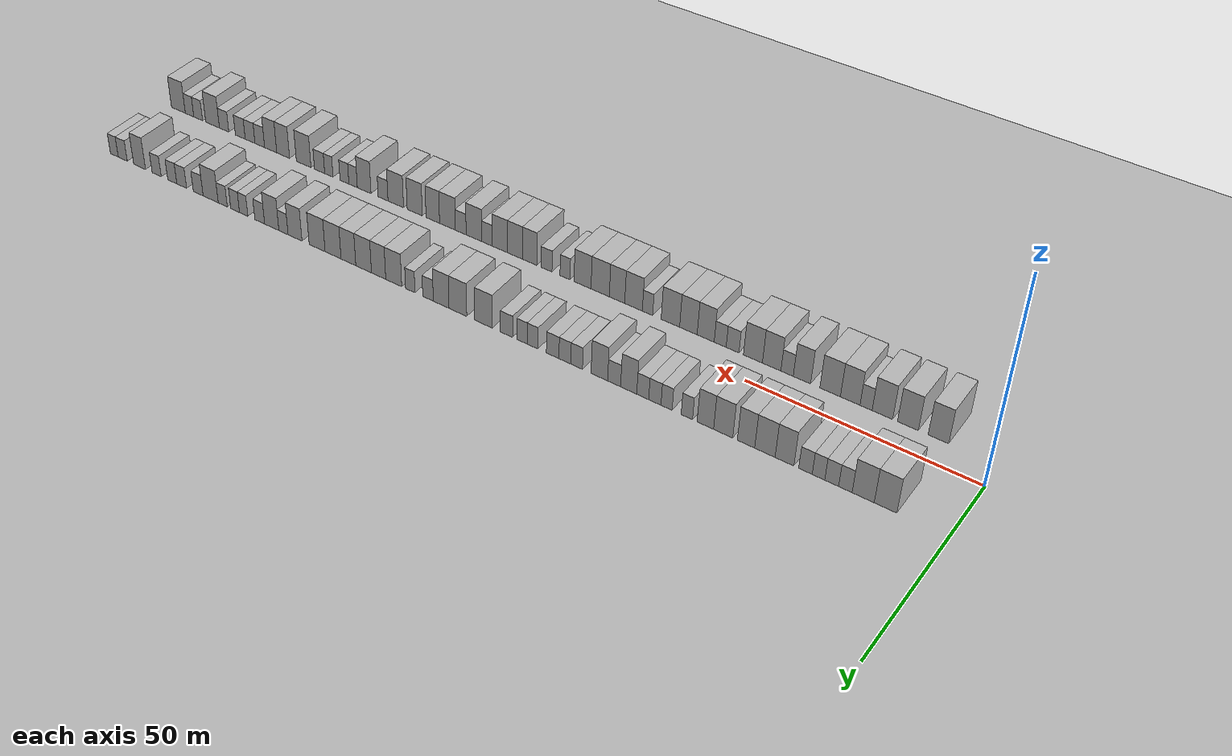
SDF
<?xml version="1.0" encoding="utf-8"?>

<sdf version="1.6">

   <world name="default">

      <gui fullscreen="0">

         <camera name="user_camera">

            <pose>-15 0 4.57585 0 0 0</pose>

            <view_controller>orbit</view_controller>

         </camera>

      </gui>

      <scene>

         <sky>

           <clouds>

             <speed>12</speed>

           </clouds>

         </sky>

         <ambient>0.4 0.4 0.4 1</ambient>

         <background>0.7 0.7 0.7 1</background>

         <shadows>1</shadows>

      </scene>

      <gravity>0 0 -9.8066</gravity>

      <magnetic_field>6e-06 2.3e-05 -4.2e-05</magnetic_field>

      <physics default="0" name="default_physics" type="ode">

         <ode>

            <solver>

               <type>quick</type>

               <iters>10</iters>

               <sor>1.0</sor>

               <use_dynamic_moi_rescaling>0</use_dynamic_moi_rescaling>

            </solver>

            <constraints>

               <cfm>0</cfm>

               <erp>0.2</erp>

               <contact_max_correcting_vel>100</contact_max_correcting_vel>

               <contact_surface_layer>0.001</contact_surface_layer>

            </constraints>

         </ode>

         <max_step_size>0.004</max_step_size>

         <real_time_factor>1</real_time_factor>

         <real_time_update_rate>250</real_time_update_rate>

      </physics>

      <light name="sun" type="directional">

         <cast_shadows>1</cast_shadows>

         <pose>0 0 10 0 0 0</pose>

         <diffuse>0.8 0.8 0.8 1</diffuse>

         <specular>0.2 0.2 0.2 1</specular>

         <attenuation>

            <range>1000</range>

            <constant>0.9</constant>

            <linear>0.01</linear>

            <quadratic>0.001</quadratic>

         </attenuation>

         <direction>-0.5 0.1 -0.9</direction>

      </light>

      <include>

         <name>ground_plane_1</name>

         <uri>model://HANNAS_ground_plane</uri>

         <pose>0 0 0  0 0 0</pose>

      </include>

      <include>

         <name>ground_plane_2</name>

         <uri>model://HANNAS_ground_plane</uri>

         <pose>100 0 0  0 0 0</pose>

      </include>

      <model name="building_1">

         <static>1</static>

         <pose frame="">12.2414 11.0000 0 0.000000 0.000000 1.570796</pose>

         <link name="link">

            <pose frame="">0 0 4.50 0 0 0</pose>

            <collision name="collision">

               <geometry>

                  <box>

                     <size>10.0000 4.4828 9.0000</size>

                  </box>

               </geometry>

               <max_contacts>10</max_contacts>

               <surface>

                  <contact>

                     <ode/>

                  </contact>

                  <bounce/>

                  <friction>

                     <torsional>

                        <ode/>

                     </torsional>

                     <ode/>

                  </friction>

               </surface>

            </collision>

            <visual name="visual">

               <cast_shadows>0</cast_shadows>

               <geometry>

                  <box>

                     <size>10.0000 4.4828 9.0000</size>

                  </box>

               </geometry>

               <material>

                  <script>

                     <uri>model://HANNAS_wall/materials/scripts</uri>

                     <uri>model://HANNAS_wall/materials/textures</uri>

                     <name>vrc/HANNAS_wall</name>

                  </script>

               </material>

            </visual>

            <self_collide>0</self_collide>

            <enable_wind>0</enable_wind>

            <kinematic>0</kinematic>

         </link>

      </model>

      <model name="building_2">

         <static>1</static>

         <pose frame="">16.7032 11.0000 0 0.000000 0.000000 1.570796</pose>

         <link name="link">

            <pose frame="">0 0 4.50 0 0 0</pose>

            <collision name="collision">

               <geometry>

                  <box>

                     <size>10.0000 4.4408 9.0000</size>

                  </box>

               </geometry>

               <max_contacts>10</max_contacts>

               <surface>

                  <contact>

                     <ode/>

                  </contact>

                  <bounce/>

                  <friction>

                     <torsional>

                        <ode/>

                     </torsional>

                     <ode/>

                  </friction>

               </surface>

            </collision>

            <visual name="visual">

               <cast_shadows>0</cast_shadows>

               <geometry>

                  <box>

                     <size>10.0000 4.4408 9.0000</size>

                  </box>

               </geometry>

               <material>

                  <script>

                     <uri>model://HANNAS_wall/materials/scripts</uri>

                     <uri>model://HANNAS_wall/materials/textures</uri>

                     <name>vrc/HANNAS_wall</name>

                  </script>

               </material>

            </visual>

            <self_collide>0</self_collide>

            <enable_wind>0</enable_wind>

            <kinematic>0</kinematic>

         </link>

      </model>

      <model name="building_3">

         <static>1</static>

         <pose frame="">20.2841 11.0000 0 0.000000 0.000000 1.570796</pose>

         <link name="link">

            <pose frame="">0 0 3.00 0 0 0</pose>

            <collision name="collision">

               <geometry>

                  <box>

                     <size>10.0000 2.7210 6.0000</size>

                  </box>

               </geometry>

               <max_contacts>10</max_contacts>

               <surface>

                  <contact>

                     <ode/>

                  </contact>

                  <bounce/>

                  <friction>

                     <torsional>

                        <ode/>

                     </torsional>

                     <ode/>

                  </friction>

               </surface>

            </collision>

            <visual name="visual">

               <cast_shadows>0</cast_shadows>

               <geometry>

                  <box>

                     <size>10.0000 2.7210 6.0000</size>

                  </box>

               </geometry>

               <material>

                  <script>

                     <uri>model://HANNAS_wall/materials/scripts</uri>

                     <uri>model://HANNAS_wall/materials/textures</uri>

                     <name>vrc/HANNAS_wall</name>

                  </script>

               </material>

            </visual>

            <self_collide>0</self_collide>

            <enable_wind>0</enable_wind>

            <kinematic>0</kinematic>

         </link>

      </model>

      <model name="building_4">

         <static>1</static>

         <pose frame="">23.0607 11.0000 0 0.000000 0.000000 1.570796</pose>

         <link name="link">

            <pose frame="">0 0 3.00 0 0 0</pose>

            <collision name="collision">

               <geometry>

                  <box>

                     <size>10.0000 2.8322 6.0000</size>

                  </box>

               </geometry>

               <max_contacts>10</max_contacts>

               <surface>

                  <contact>

                     <ode/>

                  </contact>

                  <bounce/>

                  <friction>

                     <torsional>

                        <ode/>

                     </torsional>

                     <ode/>

                  </friction>

               </surface>

            </collision>

            <visual name="visual">

               <cast_shadows>0</cast_shadows>

               <geometry>

                  <box>

                     <size>10.0000 2.8322 6.0000</size>

                  </box>

               </geometry>

               <material>

                  <script>

                     <uri>model://HANNAS_wall/materials/scripts</uri>

                     <uri>model://HANNAS_wall/materials/textures</uri>

                     <name>vrc/HANNAS_wall</name>

                  </script>

               </material>

            </visual>

            <self_collide>0</self_collide>

            <enable_wind>0</enable_wind>

            <kinematic>0</kinematic>

         </link>

      </model>

      <model name="building_5">

         <static>1</static>

         <pose frame="">25.7686 11.0000 0 0.000000 0.000000 1.570796</pose>

         <link name="link">

            <pose frame="">0 0 3.00 0 0 0</pose>

            <collision name="collision">

               <geometry>

                  <box>

                     <size>10.0000 2.5836 6.0000</size>

                  </box>

               </geometry>

               <max_contacts>10</max_contacts>

               <surface>

                  <contact>

                     <ode/>

                  </contact>

                  <bounce/>

                  <friction>

                     <torsional>

                        <ode/>

                     </torsional>

                     <ode/>

                  </friction>

               </surface>

            </collision>

            <visual name="visual">

               <cast_shadows>0</cast_shadows>

               <geometry>

                  <box>

                     <size>10.0000 2.5836 6.0000</size>

                  </box>

               </geometry>

               <material>

                  <script>

                     <uri>model://HANNAS_wall/materials/scripts</uri>

                     <uri>model://HANNAS_wall/materials/textures</uri>

                     <name>vrc/HANNAS_wall</name>

                  </script>

               </material>

            </visual>

            <self_collide>0</self_collide>

            <enable_wind>0</enable_wind>

            <kinematic>0</kinematic>

         </link>

      </model>

      <model name="building_6">

         <static>1</static>

         <pose frame="">28.4573 11.0000 0 0.000000 0.000000 1.570796</pose>

         <link name="link">

            <pose frame="">0 0 3.00 0 0 0</pose>

            <collision name="collision">

               <geometry>

                  <box>

                     <size>10.0000 2.7939 6.0000</size>

                  </box>

               </geometry>

               <max_contacts>10</max_contacts>

               <surface>

                  <contact>

                     <ode/>

                  </contact>

                  <bounce/>

                  <friction>

                     <torsional>

                        <ode/>

                     </torsional>

                     <ode/>

                  </friction>

               </surface>

            </collision>

            <visual name="visual">

               <cast_shadows>0</cast_shadows>

               <geometry>

                  <box>

                     <size>10.0000 2.7939 6.0000</size>

                  </box>

               </geometry>

               <material>

                  <script>

                     <uri>model://HANNAS_wall/materials/scripts</uri>

                     <uri>model://HANNAS_wall/materials/textures</uri>

                     <name>vrc/HANNAS_wall</name>

                  </script>

               </material>

            </visual>

            <self_collide>0</self_collide>

            <enable_wind>0</enable_wind>

            <kinematic>0</kinematic>

         </link>

      </model>

      <model name="building_7">

         <static>1</static>

         <pose frame="">32.8185 11.0000 0 0.000000 0.000000 1.570796</pose>

         <link name="link">

            <pose frame="">0 0 4.50 0 0 0</pose>

            <collision name="collision">

               <geometry>

                  <box>

                     <size>10.0000 3.9286 9.0000</size>

                  </box>

               </geometry>

               <max_contacts>10</max_contacts>

               <surface>

                  <contact>

                     <ode/>

                  </contact>

                  <bounce/>

                  <friction>

                     <torsional>

                        <ode/>

                     </torsional>

                     <ode/>

                  </friction>

               </surface>

            </collision>

            <visual name="visual">

               <cast_shadows>0</cast_shadows>

               <geometry>

                  <box>

                     <size>10.0000 3.9286 9.0000</size>

                  </box>

               </geometry>

               <material>

                  <script>

                     <uri>model://HANNAS_wall/materials/scripts</uri>

                     <uri>model://HANNAS_wall/materials/textures</uri>

                     <name>vrc/HANNAS_wall</name>

                  </script>

               </material>

            </visual>

            <self_collide>0</self_collide>

            <enable_wind>0</enable_wind>

            <kinematic>0</kinematic>

         </link>

      </model>

      <model name="building_8">

         <static>1</static>

         <pose frame="">36.9429 11.0000 0 0.000000 0.000000 1.570796</pose>

         <link name="link">

            <pose frame="">0 0 4.50 0 0 0</pose>

            <collision name="collision">

               <geometry>

                  <box>

                     <size>10.0000 4.3202 9.0000</size>

                  </box>

               </geometry>

               <max_contacts>10</max_contacts>

               <surface>

                  <contact>

                     <ode/>

                  </contact>

                  <bounce/>

                  <friction>

                     <torsional>

                        <ode/>

                     </torsional>

                     <ode/>

                  </friction>

               </surface>

            </collision>

            <visual name="visual">

               <cast_shadows>0</cast_shadows>

               <geometry>

                  <box>

                     <size>10.0000 4.3202 9.0000</size>

                  </box>

               </geometry>

               <material>

                  <script>

                     <uri>model://HANNAS_wall/materials/scripts</uri>

                     <uri>model://HANNAS_wall/materials/textures</uri>

                     <name>vrc/HANNAS_wall</name>

                  </script>

               </material>

            </visual>

            <self_collide>0</self_collide>

            <enable_wind>0</enable_wind>

            <kinematic>0</kinematic>

         </link>

      </model>

      <model name="building_9">

         <static>1</static>

         <pose frame="">40.9576 11.0000 0 0.000000 0.000000 1.570796</pose>

         <link name="link">

            <pose frame="">0 0 4.50 0 0 0</pose>

            <collision name="collision">

               <geometry>

                  <box>

                     <size>10.0000 3.7091 9.0000</size>

                  </box>

               </geometry>

               <max_contacts>10</max_contacts>

               <surface>

                  <contact>

                     <ode/>

                  </contact>

                  <bounce/>

                  <friction>

                     <torsional>

                        <ode/>

                     </torsional>

                     <ode/>

                  </friction>

               </surface>

            </collision>

            <visual name="visual">

               <cast_shadows>0</cast_shadows>

               <geometry>

                  <box>

                     <size>10.0000 3.7091 9.0000</size>

                  </box>

               </geometry>

               <material>

                  <script>

                     <uri>model://HANNAS_wall/materials/scripts</uri>

                     <uri>model://HANNAS_wall/materials/textures</uri>

                     <name>vrc/HANNAS_wall</name>

                  </script>

               </material>

            </visual>

            <self_collide>0</self_collide>

            <enable_wind>0</enable_wind>

            <kinematic>0</kinematic>

         </link>

      </model>

      <model name="building_10">

         <static>1</static>

         <pose frame="">45.8803 11.0000 0 0.000000 0.000000 1.570796</pose>

         <link name="link">

            <pose frame="">0 0 4.50 0 0 0</pose>

            <collision name="collision">

               <geometry>

                  <box>

                     <size>10.0000 4.1362 9.0000</size>

                  </box>

               </geometry>

               <max_contacts>10</max_contacts>

               <surface>

                  <contact>

                     <ode/>

                  </contact>

                  <bounce/>

                  <friction>

                     <torsional>

                        <ode/>

                     </torsional>

                     <ode/>

                  </friction>

               </surface>

            </collision>

            <visual name="visual">

               <cast_shadows>0</cast_shadows>

               <geometry>

                  <box>

                     <size>10.0000 4.1362 9.0000</size>

                  </box>

               </geometry>

               <material>

                  <script>

                     <uri>model://HANNAS_wall/materials/scripts</uri>

                     <uri>model://HANNAS_wall/materials/textures</uri>

                     <name>vrc/HANNAS_wall</name>

                  </script>

               </material>

            </visual>

            <self_collide>0</self_collide>

            <enable_wind>0</enable_wind>

            <kinematic>0</kinematic>

         </link>

      </model>

      <model name="building_11">

         <static>1</static>

         <pose frame="">49.7523 11.0000 0 0.000000 0.000000 1.570796</pose>

         <link name="link">

            <pose frame="">0 0 4.50 0 0 0</pose>

            <collision name="collision">

               <geometry>

                  <box>

                     <size>10.0000 3.6078 9.0000</size>

                  </box>

               </geometry>

               <max_contacts>10</max_contacts>

               <surface>

                  <contact>

                     <ode/>

                  </contact>

                  <bounce/>

                  <friction>

                     <torsional>

                        <ode/>

                     </torsional>

                     <ode/>

                  </friction>

               </surface>

            </collision>

            <visual name="visual">

               <cast_shadows>0</cast_shadows>

               <geometry>

                  <box>

                     <size>10.0000 3.6078 9.0000</size>

                  </box>

               </geometry>

               <material>

                  <script>

                     <uri>model://HANNAS_wall/materials/scripts</uri>

                     <uri>model://HANNAS_wall/materials/textures</uri>

                     <name>vrc/HANNAS_wall</name>

                  </script>

               </material>

            </visual>

            <self_collide>0</self_collide>

            <enable_wind>0</enable_wind>

            <kinematic>0</kinematic>

         </link>

      </model>

      <model name="building_12">

         <static>1</static>

         <pose frame="">53.8203 11.0000 0 0.000000 0.000000 1.570796</pose>

         <link name="link">

            <pose frame="">0 0 3.00 0 0 0</pose>

            <collision name="collision">

               <geometry>

                  <box>

                     <size>10.0000 2.5282 6.0000</size>

                  </box>

               </geometry>

               <max_contacts>10</max_contacts>

               <surface>

                  <contact>

                     <ode/>

                  </contact>

                  <bounce/>

                  <friction>

                     <torsional>

                        <ode/>

                     </torsional>

                     <ode/>

                  </friction>

               </surface>

            </collision>

            <visual name="visual">

               <cast_shadows>0</cast_shadows>

               <geometry>

                  <box>

                     <size>10.0000 2.5282 6.0000</size>

                  </box>

               </geometry>

               <material>

                  <script>

                     <uri>model://HANNAS_wall/materials/scripts</uri>

                     <uri>model://HANNAS_wall/materials/textures</uri>

                     <name>vrc/HANNAS_wall</name>

                  </script>

               </material>

            </visual>

            <self_collide>0</self_collide>

            <enable_wind>0</enable_wind>

            <kinematic>0</kinematic>

         </link>

      </model>

      <model name="building_13">

         <static>1</static>

         <pose frame="">58.3313 11.0000 0 0.000000 0.000000 1.570796</pose>

         <link name="link">

            <pose frame="">0 0 3.00 0 0 0</pose>

            <collision name="collision">

               <geometry>

                  <box>

                     <size>10.0000 2.4938 6.0000</size>

                  </box>

               </geometry>

               <max_contacts>10</max_contacts>

               <surface>

                  <contact>

                     <ode/>

                  </contact>

                  <bounce/>

                  <friction>

                     <torsional>

                        <ode/>

                     </torsional>

                     <ode/>

                  </friction>

               </surface>

            </collision>

            <visual name="visual">

               <cast_shadows>0</cast_shadows>

               <geometry>

                  <box>

                     <size>10.0000 2.4938 6.0000</size>

                  </box>

               </geometry>

               <material>

                  <script>

                     <uri>model://HANNAS_wall/materials/scripts</uri>

                     <uri>model://HANNAS_wall/materials/textures</uri>

                     <name>vrc/HANNAS_wall</name>

                  </script>

               </material>

            </visual>

            <self_collide>0</self_collide>

            <enable_wind>0</enable_wind>

            <kinematic>0</kinematic>

         </link>

      </model>

      <model name="building_14">

         <static>1</static>

         <pose frame="">60.9623 11.0000 0 0.000000 0.000000 1.570796</pose>

         <link name="link">

            <pose frame="">0 0 3.00 0 0 0</pose>

            <collision name="collision">

               <geometry>

                  <box>

                     <size>10.0000 2.7682 6.0000</size>

                  </box>

               </geometry>

               <max_contacts>10</max_contacts>

               <surface>

                  <contact>

                     <ode/>

                  </contact>

                  <bounce/>

                  <friction>

                     <torsional>

                        <ode/>

                     </torsional>

                     <ode/>

                  </friction>

               </surface>

            </collision>

            <visual name="visual">

               <cast_shadows>0</cast_shadows>

               <geometry>

                  <box>

                     <size>10.0000 2.7682 6.0000</size>

                  </box>

               </geometry>

               <material>

                  <script>

                     <uri>model://HANNAS_wall/materials/scripts</uri>

                     <uri>model://HANNAS_wall/materials/textures</uri>

                     <name>vrc/HANNAS_wall</name>

                  </script>

               </material>

            </visual>

            <self_collide>0</self_collide>

            <enable_wind>0</enable_wind>

            <kinematic>0</kinematic>

         </link>

      </model>

      <model name="building_15">

         <static>1</static>

         <pose frame="">63.6974 11.0000 0 0.000000 0.000000 1.570796</pose>

         <link name="link">

            <pose frame="">0 0 3.00 0 0 0</pose>

            <collision name="collision">

               <geometry>

                  <box>

                     <size>10.0000 2.7020 6.0000</size>

                  </box>

               </geometry>

               <max_contacts>10</max_contacts>

               <surface>

                  <contact>

                     <ode/>

                  </contact>

                  <bounce/>

                  <friction>

                     <torsional>

                        <ode/>

                     </torsional>

                     <ode/>

                  </friction>

               </surface>

            </collision>

            <visual name="visual">

               <cast_shadows>0</cast_shadows>

               <geometry>

                  <box>

                     <size>10.0000 2.7020 6.0000</size>

                  </box>

               </geometry>

               <material>

                  <script>

                     <uri>model://HANNAS_wall/materials/scripts</uri>

                     <uri>model://HANNAS_wall/materials/textures</uri>

                     <name>vrc/HANNAS_wall</name>

                  </script>

               </material>

            </visual>

            <self_collide>0</self_collide>

            <enable_wind>0</enable_wind>

            <kinematic>0</kinematic>

         </link>

      </model>

      <model name="building_16">

         <static>1</static>

         <pose frame="">66.8935 11.0000 0 0.000000 0.000000 1.570796</pose>

         <link name="link">

            <pose frame="">0 0 4.50 0 0 0</pose>

            <collision name="collision">

               <geometry>

                  <box>

                     <size>10.0000 3.6904 9.0000</size>

                  </box>

               </geometry>

               <max_contacts>10</max_contacts>

               <surface>

                  <contact>

                     <ode/>

                  </contact>

                  <bounce/>

                  <friction>

                     <torsional>

                        <ode/>

                     </torsional>

                     <ode/>

                  </friction>

               </surface>

            </collision>

            <visual name="visual">

               <cast_shadows>0</cast_shadows>

               <geometry>

                  <box>

                     <size>10.0000 3.6904 9.0000</size>

                  </box>

               </geometry>

               <material>

                  <script>

                     <uri>model://HANNAS_wall/materials/scripts</uri>

                     <uri>model://HANNAS_wall/materials/textures</uri>

                     <name>vrc/HANNAS_wall</name>

                  </script>

               </material>

            </visual>

            <self_collide>0</self_collide>

            <enable_wind>0</enable_wind>

            <kinematic>0</kinematic>

         </link>

      </model>

      <model name="building_17">

         <static>1</static>

         <pose frame="">70.2351 11.0000 0 0.000000 0.000000 1.570796</pose>

         <link name="link">

            <pose frame="">0 0 3.00 0 0 0</pose>

            <collision name="collision">

               <geometry>

                  <box>

                     <size>10.0000 2.9928 6.0000</size>

                  </box>

               </geometry>

               <max_contacts>10</max_contacts>

               <surface>

                  <contact>

                     <ode/>

                  </contact>

                  <bounce/>

                  <friction>

                     <torsional>

                        <ode/>

                     </torsional>

                     <ode/>

                  </friction>

               </surface>

            </collision>

            <visual name="visual">

               <cast_shadows>0</cast_shadows>

               <geometry>

                  <box>

                     <size>10.0000 2.9928 6.0000</size>

                  </box>

               </geometry>

               <material>

                  <script>

                     <uri>model://HANNAS_wall/materials/scripts</uri>

                     <uri>model://HANNAS_wall/materials/textures</uri>

                     <name>vrc/HANNAS_wall</name>

                  </script>

               </material>

            </visual>

            <self_collide>0</self_collide>

            <enable_wind>0</enable_wind>

            <kinematic>0</kinematic>

         </link>

      </model>

      <model name="building_18">

         <static>1</static>

         <pose frame="">73.6525 11.0000 0 0.000000 0.000000 1.570796</pose>

         <link name="link">

            <pose frame="">0 0 4.50 0 0 0</pose>

            <collision name="collision">

               <geometry>

                  <box>

                     <size>10.0000 3.8420 9.0000</size>

                  </box>

               </geometry>

               <max_contacts>10</max_contacts>

               <surface>

                  <contact>

                     <ode/>

                  </contact>

                  <bounce/>

                  <friction>

                     <torsional>

                        <ode/>

                     </torsional>

                     <ode/>

                  </friction>

               </surface>

            </collision>

            <visual name="visual">

               <cast_shadows>0</cast_shadows>

               <geometry>

                  <box>

                     <size>10.0000 3.8420 9.0000</size>

                  </box>

               </geometry>

               <material>

                  <script>

                     <uri>model://HANNAS_wall/materials/scripts</uri>

                     <uri>model://HANNAS_wall/materials/textures</uri>

                     <name>vrc/HANNAS_wall</name>

                  </script>

               </material>

            </visual>

            <self_collide>0</self_collide>

            <enable_wind>0</enable_wind>

            <kinematic>0</kinematic>

         </link>

      </model>

      <model name="building_19">

         <static>1</static>

         <pose frame="">78.9546 11.0000 0 0.000000 0.000000 1.570796</pose>

         <link name="link">

            <pose frame="">0 0 3.00 0 0 0</pose>

            <collision name="collision">

               <geometry>

                  <box>

                     <size>10.0000 2.7621 6.0000</size>

                  </box>

               </geometry>

               <max_contacts>10</max_contacts>

               <surface>

                  <contact>

                     <ode/>

                  </contact>

                  <bounce/>

                  <friction>

                     <torsional>

                        <ode/>

                     </torsional>

                     <ode/>

                  </friction>

               </surface>

            </collision>

            <visual name="visual">

               <cast_shadows>0</cast_shadows>

               <geometry>

                  <box>

                     <size>10.0000 2.7621 6.0000</size>

                  </box>

               </geometry>

               <material>

                  <script>

                     <uri>model://HANNAS_wall/materials/scripts</uri>

                     <uri>model://HANNAS_wall/materials/textures</uri>

                     <name>vrc/HANNAS_wall</name>

                  </script>

               </material>

            </visual>

            <self_collide>0</self_collide>

            <enable_wind>0</enable_wind>

            <kinematic>0</kinematic>

         </link>

      </model>

      <model name="building_20">

         <static>1</static>

         <pose frame="">81.7388 11.0000 0 0.000000 0.000000 1.570796</pose>

         <link name="link">

            <pose frame="">0 0 3.00 0 0 0</pose>

            <collision name="collision">

               <geometry>

                  <box>

                     <size>10.0000 2.8063 6.0000</size>

                  </box>

               </geometry>

               <max_contacts>10</max_contacts>

               <surface>

                  <contact>

                     <ode/>

                  </contact>

                  <bounce/>

                  <friction>

                     <torsional>

                        <ode/>

                     </torsional>

                     <ode/>

                  </friction>

               </surface>

            </collision>

            <visual name="visual">

               <cast_shadows>0</cast_shadows>

               <geometry>

                  <box>

                     <size>10.0000 2.8063 6.0000</size>

                  </box>

               </geometry>

               <material>

                  <script>

                     <uri>model://HANNAS_wall/materials/scripts</uri>

                     <uri>model://HANNAS_wall/materials/textures</uri>

                     <name>vrc/HANNAS_wall</name>

                  </script>

               </material>

            </visual>

            <self_collide>0</self_collide>

            <enable_wind>0</enable_wind>

            <kinematic>0</kinematic>

         </link>

      </model>

      <model name="building_21">

         <static>1</static>

         <pose frame="">84.6400 11.0000 0 0.000000 0.000000 1.570796</pose>

         <link name="link">

            <pose frame="">0 0 3.00 0 0 0</pose>

            <collision name="collision">

               <geometry>

                  <box>

                     <size>10.0000 2.9960 6.0000</size>

                  </box>

               </geometry>

               <max_contacts>10</max_contacts>

               <surface>

                  <contact>

                     <ode/>

                  </contact>

                  <bounce/>

                  <friction>

                     <torsional>

                        <ode/>

                     </torsional>

                     <ode/>

                  </friction>

               </surface>

            </collision>

            <visual name="visual">

               <cast_shadows>0</cast_shadows>

               <geometry>

                  <box>

                     <size>10.0000 2.9960 6.0000</size>

                  </box>

               </geometry>

               <material>

                  <script>

                     <uri>model://HANNAS_wall/materials/scripts</uri>

                     <uri>model://HANNAS_wall/materials/textures</uri>

                     <name>vrc/HANNAS_wall</name>

                  </script>

               </material>

            </visual>

            <self_collide>0</self_collide>

            <enable_wind>0</enable_wind>

            <kinematic>0</kinematic>

         </link>

      </model>

      <model name="building_22">

         <static>1</static>

         <pose frame="">89.4517 11.0000 0 0.000000 0.000000 1.570796</pose>

         <link name="link">

            <pose frame="">0 0 3.00 0 0 0</pose>

            <collision name="collision">

               <geometry>

                  <box>

                     <size>10.0000 2.6273 6.0000</size>

                  </box>

               </geometry>

               <max_contacts>10</max_contacts>

               <surface>

                  <contact>

                     <ode/>

                  </contact>

                  <bounce/>

                  <friction>

                     <torsional>

                        <ode/>

                     </torsional>

                     <ode/>

                  </friction>

               </surface>

            </collision>

            <visual name="visual">

               <cast_shadows>0</cast_shadows>

               <geometry>

                  <box>

                     <size>10.0000 2.6273 6.0000</size>

                  </box>

               </geometry>

               <material>

                  <script>

                     <uri>model://HANNAS_wall/materials/scripts</uri>

                     <uri>model://HANNAS_wall/materials/textures</uri>

                     <name>vrc/HANNAS_wall</name>

                  </script>

               </material>

            </visual>

            <self_collide>0</self_collide>

            <enable_wind>0</enable_wind>

            <kinematic>0</kinematic>

         </link>

      </model>

      <model name="building_23">

         <static>1</static>

         <pose frame="">92.0279 11.0000 0 0.000000 0.000000 1.570796</pose>

         <link name="link">

            <pose frame="">0 0 3.00 0 0 0</pose>

            <collision name="collision">

               <geometry>

                  <box>

                     <size>10.0000 2.5250 6.0000</size>

                  </box>

               </geometry>

               <max_contacts>10</max_contacts>

               <surface>

                  <contact>

                     <ode/>

                  </contact>

                  <bounce/>

                  <friction>

                     <torsional>

                        <ode/>

                     </torsional>

                     <ode/>

                  </friction>

               </surface>

            </collision>

            <visual name="visual">

               <cast_shadows>0</cast_shadows>

               <geometry>

                  <box>

                     <size>10.0000 2.5250 6.0000</size>

                  </box>

               </geometry>

               <material>

                  <script>

                     <uri>model://HANNAS_wall/materials/scripts</uri>

                     <uri>model://HANNAS_wall/materials/textures</uri>

                     <name>vrc/HANNAS_wall</name>

                  </script>

               </material>

            </visual>

            <self_collide>0</self_collide>

            <enable_wind>0</enable_wind>

            <kinematic>0</kinematic>

         </link>

      </model>

      <model name="building_24">

         <static>1</static>

         <pose frame="">95.7770 11.0000 0 0.000000 0.000000 1.570796</pose>

         <link name="link">

            <pose frame="">0 0 3.00 0 0 0</pose>

            <collision name="collision">

               <geometry>

                  <box>

                     <size>10.0000 2.9732 6.0000</size>

                  </box>

               </geometry>

               <max_contacts>10</max_contacts>

               <surface>

                  <contact>

                     <ode/>

                  </contact>

                  <bounce/>

                  <friction>

                     <torsional>

                        <ode/>

                     </torsional>

                     <ode/>

                  </friction>

               </surface>

            </collision>

            <visual name="visual">

               <cast_shadows>0</cast_shadows>

               <geometry>

                  <box>

                     <size>10.0000 2.9732 6.0000</size>

                  </box>

               </geometry>

               <material>

                  <script>

                     <uri>model://HANNAS_wall/materials/scripts</uri>

                     <uri>model://HANNAS_wall/materials/textures</uri>

                     <name>vrc/HANNAS_wall</name>

                  </script>

               </material>

            </visual>

            <self_collide>0</self_collide>

            <enable_wind>0</enable_wind>

            <kinematic>0</kinematic>

         </link>

      </model>

      <model name="building_25">

         <static>1</static>

         <pose frame="">101.4536 11.0000 0 0.000000 0.000000 1.570796</pose>

         <link name="link">

            <pose frame="">0 0 4.50 0 0 0</pose>

            <collision name="collision">

               <geometry>

                  <box>

                     <size>10.0000 4.3800 9.0000</size>

                  </box>

               </geometry>

               <max_contacts>10</max_contacts>

               <surface>

                  <contact>

                     <ode/>

                  </contact>

                  <bounce/>

                  <friction>

                     <torsional>

                        <ode/>

                     </torsional>

                     <ode/>

                  </friction>

               </surface>

            </collision>

            <visual name="visual">

               <cast_shadows>0</cast_shadows>

               <geometry>

                  <box>

                     <size>10.0000 4.3800 9.0000</size>

                  </box>

               </geometry>

               <material>

                  <script>

                     <uri>model://HANNAS_wall/materials/scripts</uri>

                     <uri>model://HANNAS_wall/materials/textures</uri>

                     <name>vrc/HANNAS_wall</name>

                  </script>

               </material>

            </visual>

            <self_collide>0</self_collide>

            <enable_wind>0</enable_wind>

            <kinematic>0</kinematic>

         </link>

      </model>

      <model name="building_26">

         <static>1</static>

         <pose frame="">107.8832 11.0000 0 0.000000 0.000000 1.570796</pose>

         <link name="link">

            <pose frame="">0 0 4.50 0 0 0</pose>

            <collision name="collision">

               <geometry>

                  <box>

                     <size>10.0000 4.4793 9.0000</size>

                  </box>

               </geometry>

               <max_contacts>10</max_contacts>

               <surface>

                  <contact>

                     <ode/>

                  </contact>

                  <bounce/>

                  <friction>

                     <torsional>

                        <ode/>

                     </torsional>

                     <ode/>

                  </friction>

               </surface>

            </collision>

            <visual name="visual">

               <cast_shadows>0</cast_shadows>

               <geometry>

                  <box>

                     <size>10.0000 4.4793 9.0000</size>

                  </box>

               </geometry>

               <material>

                  <script>

                     <uri>model://HANNAS_wall/materials/scripts</uri>

                     <uri>model://HANNAS_wall/materials/textures</uri>

                     <name>vrc/HANNAS_wall</name>

                  </script>

               </material>

            </visual>

            <self_collide>0</self_collide>

            <enable_wind>0</enable_wind>

            <kinematic>0</kinematic>

         </link>

      </model>

      <model name="building_27">

         <static>1</static>

         <pose frame="">112.1227 11.0000 0 0.000000 0.000000 1.570796</pose>

         <link name="link">

            <pose frame="">0 0 4.50 0 0 0</pose>

            <collision name="collision">

               <geometry>

                  <box>

                     <size>10.0000 3.9997 9.0000</size>

                  </box>

               </geometry>

               <max_contacts>10</max_contacts>

               <surface>

                  <contact>

                     <ode/>

                  </contact>

                  <bounce/>

                  <friction>

                     <torsional>

                        <ode/>

                     </torsional>

                     <ode/>

                  </friction>

               </surface>

            </collision>

            <visual name="visual">

               <cast_shadows>0</cast_shadows>

               <geometry>

                  <box>

                     <size>10.0000 3.9997 9.0000</size>

                  </box>

               </geometry>

               <material>

                  <script>

                     <uri>model://HANNAS_wall/materials/scripts</uri>

                     <uri>model://HANNAS_wall/materials/textures</uri>

                     <name>vrc/HANNAS_wall</name>

                  </script>

               </material>

            </visual>

            <self_collide>0</self_collide>

            <enable_wind>0</enable_wind>

            <kinematic>0</kinematic>

         </link>

      </model>

      <model name="building_28">

         <static>1</static>

         <pose frame="">115.4858 11.0000 0 0.000000 0.000000 1.570796</pose>

         <link name="link">

            <pose frame="">0 0 3.00 0 0 0</pose>

            <collision name="collision">

               <geometry>

                  <box>

                     <size>10.0000 2.7263 6.0000</size>

                  </box>

               </geometry>

               <max_contacts>10</max_contacts>

               <surface>

                  <contact>

                     <ode/>

                  </contact>

                  <bounce/>

                  <friction>

                     <torsional>

                        <ode/>

                     </torsional>

                     <ode/>

                  </friction>

               </surface>

            </collision>

            <visual name="visual">

               <cast_shadows>0</cast_shadows>

               <geometry>

                  <box>

                     <size>10.0000 2.7263 6.0000</size>

                  </box>

               </geometry>

               <material>

                  <script>

                     <uri>model://HANNAS_wall/materials/scripts</uri>

                     <uri>model://HANNAS_wall/materials/textures</uri>

                     <name>vrc/HANNAS_wall</name>

                  </script>

               </material>

            </visual>

            <self_collide>0</self_collide>

            <enable_wind>0</enable_wind>

            <kinematic>0</kinematic>

         </link>

      </model>

      <model name="building_29">

         <static>1</static>

         <pose frame="">120.0721 11.0000 0 0.000000 0.000000 1.570796</pose>

         <link name="link">

            <pose frame="">0 0 3.00 0 0 0</pose>

            <collision name="collision">

               <geometry>

                  <box>

                     <size>10.0000 2.4463 6.0000</size>

                  </box>

               </geometry>

               <max_contacts>10</max_contacts>

               <surface>

                  <contact>

                     <ode/>

                  </contact>

                  <bounce/>

                  <friction>

                     <torsional>

                        <ode/>

                     </torsional>

                     <ode/>

                  </friction>

               </surface>

            </collision>

            <visual name="visual">

               <cast_shadows>0</cast_shadows>

               <geometry>

                  <box>

                     <size>10.0000 2.4463 6.0000</size>

                  </box>

               </geometry>

               <material>

                  <script>

                     <uri>model://HANNAS_wall/materials/scripts</uri>

                     <uri>model://HANNAS_wall/materials/textures</uri>

                     <name>vrc/HANNAS_wall</name>

                  </script>

               </material>

            </visual>

            <self_collide>0</self_collide>

            <enable_wind>0</enable_wind>

            <kinematic>0</kinematic>

         </link>

      </model>

      <model name="building_30">

         <static>1</static>

         <pose frame="">124.3929 11.0000 0 0.000000 0.000000 1.570796</pose>

         <link name="link">

            <pose frame="">0 0 4.50 0 0 0</pose>

            <collision name="collision">

               <geometry>

                  <box>

                     <size>10.0000 4.1953 9.0000</size>

                  </box>

               </geometry>

               <max_contacts>10</max_contacts>

               <surface>

                  <contact>

                     <ode/>

                  </contact>

                  <bounce/>

                  <friction>

                     <torsional>

                        <ode/>

                     </torsional>

                     <ode/>

                  </friction>

               </surface>

            </collision>

            <visual name="visual">

               <cast_shadows>0</cast_shadows>

               <geometry>

                  <box>

                     <size>10.0000 4.1953 9.0000</size>

                  </box>

               </geometry>

               <material>

                  <script>

                     <uri>model://HANNAS_wall/materials/scripts</uri>

                     <uri>model://HANNAS_wall/materials/textures</uri>

                     <name>vrc/HANNAS_wall</name>

                  </script>

               </material>

            </visual>

            <self_collide>0</self_collide>

            <enable_wind>0</enable_wind>

            <kinematic>0</kinematic>

         </link>

      </model>

      <model name="building_31">

         <static>1</static>

         <pose frame="">128.3770 11.0000 0 0.000000 0.000000 1.570796</pose>

         <link name="link">

            <pose frame="">0 0 4.50 0 0 0</pose>

            <collision name="collision">

               <geometry>

                  <box>

                     <size>10.0000 3.7729 9.0000</size>

                  </box>

               </geometry>

               <max_contacts>10</max_contacts>

               <surface>

                  <contact>

                     <ode/>

                  </contact>

                  <bounce/>

                  <friction>

                     <torsional>

                        <ode/>

                     </torsional>

                     <ode/>

                  </friction>

               </surface>

            </collision>

            <visual name="visual">

               <cast_shadows>0</cast_shadows>

               <geometry>

                  <box>

                     <size>10.0000 3.7729 9.0000</size>

                  </box>

               </geometry>

               <material>

                  <script>

                     <uri>model://HANNAS_wall/materials/scripts</uri>

                     <uri>model://HANNAS_wall/materials/textures</uri>

                     <name>vrc/HANNAS_wall</name>

                  </script>

               </material>

            </visual>

            <self_collide>0</self_collide>

            <enable_wind>0</enable_wind>

            <kinematic>0</kinematic>

         </link>

      </model>

      <model name="building_32">

         <static>1</static>

         <pose frame="">132.3596 11.0000 0 0.000000 0.000000 1.570796</pose>

         <link name="link">

            <pose frame="">0 0 4.50 0 0 0</pose>

            <collision name="collision">

               <geometry>

                  <box>

                     <size>10.0000 4.1923 9.0000</size>

                  </box>

               </geometry>

               <max_contacts>10</max_contacts>

               <surface>

                  <contact>

                     <ode/>

                  </contact>

                  <bounce/>

                  <friction>

                     <torsional>

                        <ode/>

                     </torsional>

                     <ode/>

                  </friction>

               </surface>

            </collision>

            <visual name="visual">

               <cast_shadows>0</cast_shadows>

               <geometry>

                  <box>

                     <size>10.0000 4.1923 9.0000</size>

                  </box>

               </geometry>

               <material>

                  <script>

                     <uri>model://HANNAS_wall/materials/scripts</uri>

                     <uri>model://HANNAS_wall/materials/textures</uri>

                     <name>vrc/HANNAS_wall</name>

                  </script>

               </material>

            </visual>

            <self_collide>0</self_collide>

            <enable_wind>0</enable_wind>

            <kinematic>0</kinematic>

         </link>

      </model>

      <model name="building_33">

         <static>1</static>

         <pose frame="">136.4485 11.0000 0 0.000000 0.000000 1.570796</pose>

         <link name="link">

            <pose frame="">0 0 4.50 0 0 0</pose>

            <collision name="collision">

               <geometry>

                  <box>

                     <size>10.0000 3.9856 9.0000</size>

                  </box>

               </geometry>

               <max_contacts>10</max_contacts>

               <surface>

                  <contact>

                     <ode/>

                  </contact>

                  <bounce/>

                  <friction>

                     <torsional>

                        <ode/>

                     </torsional>

                     <ode/>

                  </friction>

               </surface>

            </collision>

            <visual name="visual">

               <cast_shadows>0</cast_shadows>

               <geometry>

                  <box>

                     <size>10.0000 3.9856 9.0000</size>

                  </box>

               </geometry>

               <material>

                  <script>

                     <uri>model://HANNAS_wall/materials/scripts</uri>

                     <uri>model://HANNAS_wall/materials/textures</uri>

                     <name>vrc/HANNAS_wall</name>

                  </script>

               </material>

            </visual>

            <self_collide>0</self_collide>

            <enable_wind>0</enable_wind>

            <kinematic>0</kinematic>

         </link>

      </model>

      <model name="building_34">

         <static>1</static>

         <pose frame="">140.6150 11.0000 0 0.000000 0.000000 1.570796</pose>

         <link name="link">

            <pose frame="">0 0 4.50 0 0 0</pose>

            <collision name="collision">

               <geometry>

                  <box>

                     <size>10.0000 4.3473 9.0000</size>

                  </box>

               </geometry>

               <max_contacts>10</max_contacts>

               <surface>

                  <contact>

                     <ode/>

                  </contact>

                  <bounce/>

                  <friction>

                     <torsional>

                        <ode/>

                     </torsional>

                     <ode/>

                  </friction>

               </surface>

            </collision>

            <visual name="visual">

               <cast_shadows>0</cast_shadows>

               <geometry>

                  <box>

                     <size>10.0000 4.3473 9.0000</size>

                  </box>

               </geometry>

               <material>

                  <script>

                     <uri>model://HANNAS_wall/materials/scripts</uri>

                     <uri>model://HANNAS_wall/materials/textures</uri>

                     <name>vrc/HANNAS_wall</name>

                  </script>

               </material>

            </visual>

            <self_collide>0</self_collide>

            <enable_wind>0</enable_wind>

            <kinematic>0</kinematic>

         </link>

      </model>

      <model name="building_35">

         <static>1</static>

         <pose frame="">144.9745 11.0000 0 0.000000 0.000000 1.570796</pose>

         <link name="link">

            <pose frame="">0 0 4.50 0 0 0</pose>

            <collision name="collision">

               <geometry>

                  <box>

                     <size>10.0000 4.3716 9.0000</size>

                  </box>

               </geometry>

               <max_contacts>10</max_contacts>

               <surface>

                  <contact>

                     <ode/>

                  </contact>

                  <bounce/>

                  <friction>

                     <torsional>

                        <ode/>

                     </torsional>

                     <ode/>

                  </friction>

               </surface>

            </collision>

            <visual name="visual">

               <cast_shadows>0</cast_shadows>

               <geometry>

                  <box>

                     <size>10.0000 4.3716 9.0000</size>

                  </box>

               </geometry>

               <material>

                  <script>

                     <uri>model://HANNAS_wall/materials/scripts</uri>

                     <uri>model://HANNAS_wall/materials/textures</uri>

                     <name>vrc/HANNAS_wall</name>

                  </script>

               </material>

            </visual>

            <self_collide>0</self_collide>

            <enable_wind>0</enable_wind>

            <kinematic>0</kinematic>

         </link>

      </model>

      <model name="building_36">

         <static>1</static>

         <pose frame="">151.1063 11.0000 0 0.000000 0.000000 1.570796</pose>

         <link name="link">

            <pose frame="">0 0 4.50 0 0 0</pose>

            <collision name="collision">

               <geometry>

                  <box>

                     <size>10.0000 3.8922 9.0000</size>

                  </box>

               </geometry>

               <max_contacts>10</max_contacts>

               <surface>

                  <contact>

                     <ode/>

                  </contact>

                  <bounce/>

                  <friction>

                     <torsional>

                        <ode/>

                     </torsional>

                     <ode/>

                  </friction>

               </surface>

            </collision>

            <visual name="visual">

               <cast_shadows>0</cast_shadows>

               <geometry>

                  <box>

                     <size>10.0000 3.8922 9.0000</size>

                  </box>

               </geometry>

               <material>

                  <script>

                     <uri>model://HANNAS_wall/materials/scripts</uri>

                     <uri>model://HANNAS_wall/materials/textures</uri>

                     <name>vrc/HANNAS_wall</name>

                  </script>

               </material>

            </visual>

            <self_collide>0</self_collide>

            <enable_wind>0</enable_wind>

            <kinematic>0</kinematic>

         </link>

      </model>

      <model name="building_37">

         <static>1</static>

         <pose frame="">154.3413 11.0000 0 0.000000 0.000000 1.570796</pose>

         <link name="link">

            <pose frame="">0 0 3.00 0 0 0</pose>

            <collision name="collision">

               <geometry>

                  <box>

                     <size>10.0000 2.5777 6.0000</size>

                  </box>

               </geometry>

               <max_contacts>10</max_contacts>

               <surface>

                  <contact>

                     <ode/>

                  </contact>

                  <bounce/>

                  <friction>

                     <torsional>

                        <ode/>

                     </torsional>

                     <ode/>

                  </friction>

               </surface>

            </collision>

            <visual name="visual">

               <cast_shadows>0</cast_shadows>

               <geometry>

                  <box>

                     <size>10.0000 2.5777 6.0000</size>

                  </box>

               </geometry>

               <material>

                  <script>

                     <uri>model://HANNAS_wall/materials/scripts</uri>

                     <uri>model://HANNAS_wall/materials/textures</uri>

                     <name>vrc/HANNAS_wall</name>

                  </script>

               </material>

            </visual>

            <self_collide>0</self_collide>

            <enable_wind>0</enable_wind>

            <kinematic>0</kinematic>

         </link>

      </model>

      <model name="building_38">

         <static>1</static>

         <pose frame="">157.6521 11.0000 0 0.000000 0.000000 1.570796</pose>

         <link name="link">

            <pose frame="">0 0 4.50 0 0 0</pose>

            <collision name="collision">

               <geometry>

                  <box>

                     <size>10.0000 4.0439 9.0000</size>

                  </box>

               </geometry>

               <max_contacts>10</max_contacts>

               <surface>

                  <contact>

                     <ode/>

                  </contact>

                  <bounce/>

                  <friction>

                     <torsional>

                        <ode/>

                     </torsional>

                     <ode/>

                  </friction>

               </surface>

            </collision>

            <visual name="visual">

               <cast_shadows>0</cast_shadows>

               <geometry>

                  <box>

                     <size>10.0000 4.0439 9.0000</size>

                  </box>

               </geometry>

               <material>

                  <script>

                     <uri>model://HANNAS_wall/materials/scripts</uri>

                     <uri>model://HANNAS_wall/materials/textures</uri>

                     <name>vrc/HANNAS_wall</name>

                  </script>

               </material>

            </visual>

            <self_collide>0</self_collide>

            <enable_wind>0</enable_wind>

            <kinematic>0</kinematic>

         </link>

      </model>

      <model name="building_39">

         <static>1</static>

         <pose frame="">161.0663 11.0000 0 0.000000 0.000000 1.570796</pose>

         <link name="link">

            <pose frame="">0 0 3.00 0 0 0</pose>

            <collision name="collision">

               <geometry>

                  <box>

                     <size>10.0000 2.7846 6.0000</size>

                  </box>

               </geometry>

               <max_contacts>10</max_contacts>

               <surface>

                  <contact>

                     <ode/>

                  </contact>

                  <bounce/>

                  <friction>

                     <torsional>

                        <ode/>

                     </torsional>

                     <ode/>

                  </friction>

               </surface>

            </collision>

            <visual name="visual">

               <cast_shadows>0</cast_shadows>

               <geometry>

                  <box>

                     <size>10.0000 2.7846 6.0000</size>

                  </box>

               </geometry>

               <material>

                  <script>

                     <uri>model://HANNAS_wall/materials/scripts</uri>

                     <uri>model://HANNAS_wall/materials/textures</uri>

                     <name>vrc/HANNAS_wall</name>

                  </script>

               </material>

            </visual>

            <self_collide>0</self_collide>

            <enable_wind>0</enable_wind>

            <kinematic>0</kinematic>

         </link>

      </model>

      <model name="building_40">

         <static>1</static>

         <pose frame="">165.6680 11.0000 0 0.000000 0.000000 1.570796</pose>

         <link name="link">

            <pose frame="">0 0 3.00 0 0 0</pose>

            <collision name="collision">

               <geometry>

                  <box>

                     <size>10.0000 2.4186 6.0000</size>

                  </box>

               </geometry>

               <max_contacts>10</max_contacts>

               <surface>

                  <contact>

                     <ode/>

                  </contact>

                  <bounce/>

                  <friction>

                     <torsional>

                        <ode/>

                     </torsional>

                     <ode/>

                  </friction>

               </surface>

            </collision>

            <visual name="visual">

               <cast_shadows>0</cast_shadows>

               <geometry>

                  <box>

                     <size>10.0000 2.4186 6.0000</size>

                  </box>

               </geometry>

               <material>

                  <script>

                     <uri>model://HANNAS_wall/materials/scripts</uri>

                     <uri>model://HANNAS_wall/materials/textures</uri>

                     <name>vrc/HANNAS_wall</name>

                  </script>

               </material>

            </visual>

            <self_collide>0</self_collide>

            <enable_wind>0</enable_wind>

            <kinematic>0</kinematic>

         </link>

      </model>

      <model name="building_41">

         <static>1</static>

         <pose frame="">168.1445 11.0000 0 0.000000 0.000000 1.570796</pose>

         <link name="link">

            <pose frame="">0 0 3.00 0 0 0</pose>

            <collision name="collision">

               <geometry>

                  <box>

                     <size>10.0000 2.5344 6.0000</size>

                  </box>

               </geometry>

               <max_contacts>10</max_contacts>

               <surface>

                  <contact>

                     <ode/>

                  </contact>

                  <bounce/>

                  <friction>

                     <torsional>

                        <ode/>

                     </torsional>

                     <ode/>

                  </friction>

               </surface>

            </collision>

            <visual name="visual">

               <cast_shadows>0</cast_shadows>

               <geometry>

                  <box>

                     <size>10.0000 2.5344 6.0000</size>

                  </box>

               </geometry>

               <material>

                  <script>

                     <uri>model://HANNAS_wall/materials/scripts</uri>

                     <uri>model://HANNAS_wall/materials/textures</uri>

                     <name>vrc/HANNAS_wall</name>

                  </script>

               </material>

            </visual>

            <self_collide>0</self_collide>

            <enable_wind>0</enable_wind>

            <kinematic>0</kinematic>

         </link>

      </model>

      <model name="building_42">

         <static>1</static>

         <pose frame="">171.7299 11.0000 0 0.000000 0.000000 1.570796</pose>

         <link name="link">

            <pose frame="">0 0 3.00 0 0 0</pose>

            <collision name="collision">

               <geometry>

                  <box>

                     <size>10.0000 2.6363 6.0000</size>

                  </box>

               </geometry>

               <max_contacts>10</max_contacts>

               <surface>

                  <contact>

                     <ode/>

                  </contact>

                  <bounce/>

                  <friction>

                     <torsional>

                        <ode/>

                     </torsional>

                     <ode/>

                  </friction>

               </surface>

            </collision>

            <visual name="visual">

               <cast_shadows>0</cast_shadows>

               <geometry>

                  <box>

                     <size>10.0000 2.6363 6.0000</size>

                  </box>

               </geometry>

               <material>

                  <script>

                     <uri>model://HANNAS_wall/materials/scripts</uri>

                     <uri>model://HANNAS_wall/materials/textures</uri>

                     <name>vrc/HANNAS_wall</name>

                  </script>

               </material>

            </visual>

            <self_collide>0</self_collide>

            <enable_wind>0</enable_wind>

            <kinematic>0</kinematic>

         </link>

      </model>

      <model name="building_43">

         <static>1</static>

         <pose frame="">175.2818 11.0000 0 0.000000 0.000000 1.570796</pose>

         <link name="link">

            <pose frame="">0 0 4.50 0 0 0</pose>

            <collision name="collision">

               <geometry>

                  <box>

                     <size>10.0000 4.4676 9.0000</size>

                  </box>

               </geometry>

               <max_contacts>10</max_contacts>

               <surface>

                  <contact>

                     <ode/>

                  </contact>

                  <bounce/>

                  <friction>

                     <torsional>

                        <ode/>

                     </torsional>

                     <ode/>

                  </friction>

               </surface>

            </collision>

            <visual name="visual">

               <cast_shadows>0</cast_shadows>

               <geometry>

                  <box>

                     <size>10.0000 4.4676 9.0000</size>

                  </box>

               </geometry>

               <material>

                  <script>

                     <uri>model://HANNAS_wall/materials/scripts</uri>

                     <uri>model://HANNAS_wall/materials/textures</uri>

                     <name>vrc/HANNAS_wall</name>

                  </script>

               </material>

            </visual>

            <self_collide>0</self_collide>

            <enable_wind>0</enable_wind>

            <kinematic>0</kinematic>

         </link>

      </model>

      <model name="building_44">

         <static>1</static>

         <pose frame="">178.9684 11.0000 0 0.000000 0.000000 1.570796</pose>

         <link name="link">

            <pose frame="">0 0 3.00 0 0 0</pose>

            <collision name="collision">

               <geometry>

                  <box>

                     <size>10.0000 2.9055 6.0000</size>

                  </box>

               </geometry>

               <max_contacts>10</max_contacts>

               <surface>

                  <contact>

                     <ode/>

                  </contact>

                  <bounce/>

                  <friction>

                     <torsional>

                        <ode/>

                     </torsional>

                     <ode/>

                  </friction>

               </surface>

            </collision>

            <visual name="visual">

               <cast_shadows>0</cast_shadows>

               <geometry>

                  <box>

                     <size>10.0000 2.9055 6.0000</size>

                  </box>

               </geometry>

               <material>

                  <script>

                     <uri>model://HANNAS_wall/materials/scripts</uri>

                     <uri>model://HANNAS_wall/materials/textures</uri>

                     <name>vrc/HANNAS_wall</name>

                  </script>

               </material>

            </visual>

            <self_collide>0</self_collide>

            <enable_wind>0</enable_wind>

            <kinematic>0</kinematic>

         </link>

      </model>

      <model name="building_45">

         <static>1</static>

         <pose frame="">183.8942 11.0000 0 0.000000 0.000000 1.570796</pose>

         <link name="link">

            <pose frame="">0 0 3.00 0 0 0</pose>

            <collision name="collision">

               <geometry>

                  <box>

                     <size>10.0000 2.9461 6.0000</size>

                  </box>

               </geometry>

               <max_contacts>10</max_contacts>

               <surface>

                  <contact>

                     <ode/>

                  </contact>

                  <bounce/>

                  <friction>

                     <torsional>

                        <ode/>

                     </torsional>

                     <ode/>

                  </friction>

               </surface>

            </collision>

            <visual name="visual">

               <cast_shadows>0</cast_shadows>

               <geometry>

                  <box>

                     <size>10.0000 2.9461 6.0000</size>

                  </box>

               </geometry>

               <material>

                  <script>

                     <uri>model://HANNAS_wall/materials/scripts</uri>

                     <uri>model://HANNAS_wall/materials/textures</uri>

                     <name>vrc/HANNAS_wall</name>

                  </script>

               </material>

            </visual>

            <self_collide>0</self_collide>

            <enable_wind>0</enable_wind>

            <kinematic>0</kinematic>

         </link>

      </model>

      <model name="building_46">

         <static>1</static>

         <pose frame="">186.7300 11.0000 0 0.000000 0.000000 1.570796</pose>

         <link name="link">

            <pose frame="">0 0 3.00 0 0 0</pose>

            <collision name="collision">

               <geometry>

                  <box>

                     <size>10.0000 2.7256 6.0000</size>

                  </box>

               </geometry>

               <max_contacts>10</max_contacts>

               <surface>

                  <contact>

                     <ode/>

                  </contact>

                  <bounce/>

                  <friction>

                     <torsional>

                        <ode/>

                     </torsional>

                     <ode/>

                  </friction>

               </surface>

            </collision>

            <visual name="visual">

               <cast_shadows>0</cast_shadows>

               <geometry>

                  <box>

                     <size>10.0000 2.7256 6.0000</size>

                  </box>

               </geometry>

               <material>

                  <script>

                     <uri>model://HANNAS_wall/materials/scripts</uri>

                     <uri>model://HANNAS_wall/materials/textures</uri>

                     <name>vrc/HANNAS_wall</name>

                  </script>

               </material>

            </visual>

            <self_collide>0</self_collide>

            <enable_wind>0</enable_wind>

            <kinematic>0</kinematic>

         </link>

      </model>

      <model name="building_47">

         <static>1</static>

         <pose frame="">191.4813 11.0000 0 0.000000 0.000000 1.570796</pose>

         <link name="link">

            <pose frame="">0 0 3.00 0 0 0</pose>

            <collision name="collision">

               <geometry>

                  <box>

                     <size>10.0000 2.7770 6.0000</size>

                  </box>

               </geometry>

               <max_contacts>10</max_contacts>

               <surface>

                  <contact>

                     <ode/>

                  </contact>

                  <bounce/>

                  <friction>

                     <torsional>

                        <ode/>

                     </torsional>

                     <ode/>

                  </friction>

               </surface>

            </collision>

            <visual name="visual">

               <cast_shadows>0</cast_shadows>

               <geometry>

                  <box>

                     <size>10.0000 2.7770 6.0000</size>

                  </box>

               </geometry>

               <material>

                  <script>

                     <uri>model://HANNAS_wall/materials/scripts</uri>

                     <uri>model://HANNAS_wall/materials/textures</uri>

                     <name>vrc/HANNAS_wall</name>

                  </script>

               </material>

            </visual>

            <self_collide>0</self_collide>

            <enable_wind>0</enable_wind>

            <kinematic>0</kinematic>

         </link>

      </model>

      <model name="building_48">

         <static>1</static>

         <pose frame="">196.7020 11.0000 0 0.000000 0.000000 1.570796</pose>

         <link name="link">

            <pose frame="">0 0 4.50 0 0 0</pose>

            <collision name="collision">

               <geometry>

                  <box>

                     <size>10.0000 3.6644 9.0000</size>

                  </box>

               </geometry>

               <max_contacts>10</max_contacts>

               <surface>

                  <contact>

                     <ode/>

                  </contact>

                  <bounce/>

                  <friction>

                     <torsional>

                        <ode/>

                     </torsional>

                     <ode/>

                  </friction>

               </surface>

            </collision>

            <visual name="visual">

               <cast_shadows>0</cast_shadows>

               <geometry>

                  <box>

                     <size>10.0000 3.6644 9.0000</size>

                  </box>

               </geometry>

               <material>

                  <script>

                     <uri>model://HANNAS_wall/materials/scripts</uri>

                     <uri>model://HANNAS_wall/materials/textures</uri>

                     <name>vrc/HANNAS_wall</name>

                  </script>

               </material>

            </visual>

            <self_collide>0</self_collide>

            <enable_wind>0</enable_wind>

            <kinematic>0</kinematic>

         </link>

      </model>

      <model name="building_49">

         <static>1</static>

         <pose frame="">201.9401 11.0000 0 0.000000 0.000000 1.570796</pose>

         <link name="link">

            <pose frame="">0 0 3.00 0 0 0</pose>

            <collision name="collision">

               <geometry>

                  <box>

                     <size>10.0000 2.8118 6.0000</size>

                  </box>

               </geometry>

               <max_contacts>10</max_contacts>

               <surface>

                  <contact>

                     <ode/>

                  </contact>

                  <bounce/>

                  <friction>

                     <torsional>

                        <ode/>

                     </torsional>

                     <ode/>

                  </friction>

               </surface>

            </collision>

            <visual name="visual">

               <cast_shadows>0</cast_shadows>

               <geometry>

                  <box>

                     <size>10.0000 2.8118 6.0000</size>

                  </box>

               </geometry>

               <material>

                  <script>

                     <uri>model://HANNAS_wall/materials/scripts</uri>

                     <uri>model://HANNAS_wall/materials/textures</uri>

                     <name>vrc/HANNAS_wall</name>

                  </script>

               </material>

            </visual>

            <self_collide>0</self_collide>

            <enable_wind>0</enable_wind>

            <kinematic>0</kinematic>

         </link>

      </model>

      <model name="building_50">

         <static>1</static>

         <pose frame="">204.5741 11.0000 0 0.000000 0.000000 1.570796</pose>

         <link name="link">

            <pose frame="">0 0 3.00 0 0 0</pose>

            <collision name="collision">

               <geometry>

                  <box>

                     <size>10.0000 2.4562 6.0000</size>

                  </box>

               </geometry>

               <max_contacts>10</max_contacts>

               <surface>

                  <contact>

                     <ode/>

                  </contact>

                  <bounce/>

                  <friction>

                     <torsional>

                        <ode/>

                     </torsional>

                     <ode/>

                  </friction>

               </surface>

            </collision>

            <visual name="visual">

               <cast_shadows>0</cast_shadows>

               <geometry>

                  <box>

                     <size>10.0000 2.4562 6.0000</size>

                  </box>

               </geometry>

               <material>

                  <script>

                     <uri>model://HANNAS_wall/materials/scripts</uri>

                     <uri>model://HANNAS_wall/materials/textures</uri>

                     <name>vrc/HANNAS_wall</name>

                  </script>

               </material>

            </visual>

            <self_collide>0</self_collide>

            <enable_wind>0</enable_wind>

            <kinematic>0</kinematic>

         </link>

      </model>

      <model name="building_51">

         <static>1</static>

         <pose frame="">12.0988 -11.0000 0 0.000000 0.000000 1.570796</pose>

         <link name="link">

            <pose frame="">0 0 4.50 0 0 0</pose>

            <collision name="collision">

               <geometry>

                  <box>

                     <size>10.0000 4.1976 9.0000</size>

                  </box>

               </geometry>

               <max_contacts>10</max_contacts>

               <surface>

                  <contact>

                     <ode/>

                  </contact>

                  <bounce/>

                  <friction>

                     <torsional>

                        <ode/>

                     </torsional>

                     <ode/>

                  </friction>

               </surface>

            </collision>

            <visual name="visual">

               <cast_shadows>0</cast_shadows>

               <geometry>

                  <box>

                     <size>10.0000 4.1976 9.0000</size>

                  </box>

               </geometry>

               <material>

                  <script>

                     <uri>model://HANNAS_wall/materials/scripts</uri>

                     <uri>model://HANNAS_wall/materials/textures</uri>

                     <name>vrc/HANNAS_wall</name>

                  </script>

               </material>

            </visual>

            <self_collide>0</self_collide>

            <enable_wind>0</enable_wind>

            <kinematic>0</kinematic>

         </link>

      </model>

      <model name="building_52">

         <static>1</static>

         <pose frame="">18.3634 -11.0000 0 0.000000 0.000000 1.570796</pose>

         <link name="link">

            <pose frame="">0 0 4.50 0 0 0</pose>

            <collision name="collision">

               <geometry>

                  <box>

                     <size>10.0000 4.3317 9.0000</size>

                  </box>

               </geometry>

               <max_contacts>10</max_contacts>

               <surface>

                  <contact>

                     <ode/>

                  </contact>

                  <bounce/>

                  <friction>

                     <torsional>

                        <ode/>

                     </torsional>

                     <ode/>

                  </friction>

               </surface>

            </collision>

            <visual name="visual">

               <cast_shadows>0</cast_shadows>

               <geometry>

                  <box>

                     <size>10.0000 4.3317 9.0000</size>

                  </box>

               </geometry>

               <material>

                  <script>

                     <uri>model://HANNAS_wall/materials/scripts</uri>

                     <uri>model://HANNAS_wall/materials/textures</uri>

                     <name>vrc/HANNAS_wall</name>

                  </script>

               </material>

            </visual>

            <self_collide>0</self_collide>

            <enable_wind>0</enable_wind>

            <kinematic>0</kinematic>

         </link>

      </model>

      <model name="building_53">

         <static>1</static>

         <pose frame="">23.6834 -11.0000 0 0.000000 0.000000 1.570796</pose>

         <link name="link">

            <pose frame="">0 0 4.50 0 0 0</pose>

            <collision name="collision">

               <geometry>

                  <box>

                     <size>10.0000 4.3081 9.0000</size>

                  </box>

               </geometry>

               <max_contacts>10</max_contacts>

               <surface>

                  <contact>

                     <ode/>

                  </contact>

                  <bounce/>

                  <friction>

                     <torsional>

                        <ode/>

                     </torsional>

                     <ode/>

                  </friction>

               </surface>

            </collision>

            <visual name="visual">

               <cast_shadows>0</cast_shadows>

               <geometry>

                  <box>

                     <size>10.0000 4.3081 9.0000</size>

                  </box>

               </geometry>

               <material>

                  <script>

                     <uri>model://HANNAS_wall/materials/scripts</uri>

                     <uri>model://HANNAS_wall/materials/textures</uri>

                     <name>vrc/HANNAS_wall</name>

                  </script>

               </material>

            </visual>

            <self_collide>0</self_collide>

            <enable_wind>0</enable_wind>

            <kinematic>0</kinematic>

         </link>

      </model>

      <model name="building_54">

         <static>1</static>

         <pose frame="">27.1206 -11.0000 0 0.000000 0.000000 1.570796</pose>

         <link name="link">

            <pose frame="">0 0 3.00 0 0 0</pose>

            <collision name="collision">

               <geometry>

                  <box>

                     <size>10.0000 2.5663 6.0000</size>

                  </box>

               </geometry>

               <max_contacts>10</max_contacts>

               <surface>

                  <contact>

                     <ode/>

                  </contact>

                  <bounce/>

                  <friction>

                     <torsional>

                        <ode/>

                     </torsional>

                     <ode/>

                  </friction>

               </surface>

            </collision>

            <visual name="visual">

               <cast_shadows>0</cast_shadows>

               <geometry>

                  <box>

                     <size>10.0000 2.5663 6.0000</size>

                  </box>

               </geometry>

               <material>

                  <script>

                     <uri>model://HANNAS_wall/materials/scripts</uri>

                     <uri>model://HANNAS_wall/materials/textures</uri>

                     <name>vrc/HANNAS_wall</name>

                  </script>

               </material>

            </visual>

            <self_collide>0</self_collide>

            <enable_wind>0</enable_wind>

            <kinematic>0</kinematic>

         </link>

      </model>

      <model name="building_55">

         <static>1</static>

         <pose frame="">30.4940 -11.0000 0 0.000000 0.000000 1.570796</pose>

         <link name="link">

            <pose frame="">0 0 4.50 0 0 0</pose>

            <collision name="collision">

               <geometry>

                  <box>

                     <size>10.0000 4.1804 9.0000</size>

                  </box>

               </geometry>

               <max_contacts>10</max_contacts>

               <surface>

                  <contact>

                     <ode/>

                  </contact>

                  <bounce/>

                  <friction>

                     <torsional>

                        <ode/>

                     </torsional>

                     <ode/>

                  </friction>

               </surface>

            </collision>

            <visual name="visual">

               <cast_shadows>0</cast_shadows>

               <geometry>

                  <box>

                     <size>10.0000 4.1804 9.0000</size>

                  </box>

               </geometry>

               <material>

                  <script>

                     <uri>model://HANNAS_wall/materials/scripts</uri>

                     <uri>model://HANNAS_wall/materials/textures</uri>

                     <name>vrc/HANNAS_wall</name>

                  </script>

               </material>

            </visual>

            <self_collide>0</self_collide>

            <enable_wind>0</enable_wind>

            <kinematic>0</kinematic>

         </link>

      </model>

      <model name="building_56">

         <static>1</static>

         <pose frame="">34.8016 -11.0000 0 0.000000 0.000000 1.570796</pose>

         <link name="link">

            <pose frame="">0 0 4.50 0 0 0</pose>

            <collision name="collision">

               <geometry>

                  <box>

                     <size>10.0000 4.4348 9.0000</size>

                  </box>

               </geometry>

               <max_contacts>10</max_contacts>

               <surface>

                  <contact>

                     <ode/>

                  </contact>

                  <bounce/>

                  <friction>

                     <torsional>

                        <ode/>

                     </torsional>

                     <ode/>

                  </friction>

               </surface>

            </collision>

            <visual name="visual">

               <cast_shadows>0</cast_shadows>

               <geometry>

                  <box>

                     <size>10.0000 4.4348 9.0000</size>

                  </box>

               </geometry>

               <material>

                  <script>

                     <uri>model://HANNAS_wall/materials/scripts</uri>

                     <uri>model://HANNAS_wall/materials/textures</uri>

                     <name>vrc/HANNAS_wall</name>

                  </script>

               </material>

            </visual>

            <self_collide>0</self_collide>

            <enable_wind>0</enable_wind>

            <kinematic>0</kinematic>

         </link>

      </model>

      <model name="building_57">

         <static>1</static>

         <pose frame="">40.9238 -11.0000 0 0.000000 0.000000 1.570796</pose>

         <link name="link">

            <pose frame="">0 0 4.50 0 0 0</pose>

            <collision name="collision">

               <geometry>

                  <box>

                     <size>10.0000 3.8095 9.0000</size>

                  </box>

               </geometry>

               <max_contacts>10</max_contacts>

               <surface>

                  <contact>

                     <ode/>

                  </contact>

                  <bounce/>

                  <friction>

                     <torsional>

                        <ode/>

                     </torsional>

                     <ode/>

                  </friction>

               </surface>

            </collision>

            <visual name="visual">

               <cast_shadows>0</cast_shadows>

               <geometry>

                  <box>

                     <size>10.0000 3.8095 9.0000</size>

                  </box>

               </geometry>

               <material>

                  <script>

                     <uri>model://HANNAS_wall/materials/scripts</uri>

                     <uri>model://HANNAS_wall/materials/textures</uri>

                     <name>vrc/HANNAS_wall</name>

                  </script>

               </material>

            </visual>

            <self_collide>0</self_collide>

            <enable_wind>0</enable_wind>

            <kinematic>0</kinematic>

         </link>

      </model>

      <model name="building_58">

         <static>1</static>

         <pose frame="">44.1946 -11.0000 0 0.000000 0.000000 1.570796</pose>

         <link name="link">

            <pose frame="">0 0 3.00 0 0 0</pose>

            <collision name="collision">

               <geometry>

                  <box>

                     <size>10.0000 2.7320 6.0000</size>

                  </box>

               </geometry>

               <max_contacts>10</max_contacts>

               <surface>

                  <contact>

                     <ode/>

                  </contact>

                  <bounce/>

                  <friction>

                     <torsional>

                        <ode/>

                     </torsional>

                     <ode/>

                  </friction>

               </surface>

            </collision>

            <visual name="visual">

               <cast_shadows>0</cast_shadows>

               <geometry>

                  <box>

                     <size>10.0000 2.7320 6.0000</size>

                  </box>

               </geometry>

               <material>

                  <script>

                     <uri>model://HANNAS_wall/materials/scripts</uri>

                     <uri>model://HANNAS_wall/materials/textures</uri>

                     <name>vrc/HANNAS_wall</name>

                  </script>

               </material>

            </visual>

            <self_collide>0</self_collide>

            <enable_wind>0</enable_wind>

            <kinematic>0</kinematic>

         </link>

      </model>

      <model name="building_59">

         <static>1</static>

         <pose frame="">47.6147 -11.0000 0 0.000000 0.000000 1.570796</pose>

         <link name="link">

            <pose frame="">0 0 4.50 0 0 0</pose>

            <collision name="collision">

               <geometry>

                  <box>

                     <size>10.0000 4.1082 9.0000</size>

                  </box>

               </geometry>

               <max_contacts>10</max_contacts>

               <surface>

                  <contact>

                     <ode/>

                  </contact>

                  <bounce/>

                  <friction>

                     <torsional>

                        <ode/>

                     </torsional>

                     <ode/>

                  </friction>

               </surface>

            </collision>

            <visual name="visual">

               <cast_shadows>0</cast_shadows>

               <geometry>

                  <box>

                     <size>10.0000 4.1082 9.0000</size>

                  </box>

               </geometry>

               <material>

                  <script>

                     <uri>model://HANNAS_wall/materials/scripts</uri>

                     <uri>model://HANNAS_wall/materials/textures</uri>

                     <name>vrc/HANNAS_wall</name>

                  </script>

               </material>

            </visual>

            <self_collide>0</self_collide>

            <enable_wind>0</enable_wind>

            <kinematic>0</kinematic>

         </link>

      </model>

      <model name="building_60">

         <static>1</static>

         <pose frame="">51.8039 -11.0000 0 0.000000 0.000000 1.570796</pose>

         <link name="link">

            <pose frame="">0 0 4.50 0 0 0</pose>

            <collision name="collision">

               <geometry>

                  <box>

                     <size>10.0000 4.2702 9.0000</size>

                  </box>

               </geometry>

               <max_contacts>10</max_contacts>

               <surface>

                  <contact>

                     <ode/>

                  </contact>

                  <bounce/>

                  <friction>

                     <torsional>

                        <ode/>

                     </torsional>

                     <ode/>

                  </friction>

               </surface>

            </collision>

            <visual name="visual">

               <cast_shadows>0</cast_shadows>

               <geometry>

                  <box>

                     <size>10.0000 4.2702 9.0000</size>

                  </box>

               </geometry>

               <material>

                  <script>

                     <uri>model://HANNAS_wall/materials/scripts</uri>

                     <uri>model://HANNAS_wall/materials/textures</uri>

                     <name>vrc/HANNAS_wall</name>

                  </script>

               </material>

            </visual>

            <self_collide>0</self_collide>

            <enable_wind>0</enable_wind>

            <kinematic>0</kinematic>

         </link>

      </model>

      <model name="building_61">

         <static>1</static>

         <pose frame="">56.4022 -11.0000 0 0.000000 0.000000 1.570796</pose>

         <link name="link">

            <pose frame="">0 0 3.00 0 0 0</pose>

            <collision name="collision">

               <geometry>

                  <box>

                     <size>10.0000 2.9265 6.0000</size>

                  </box>

               </geometry>

               <max_contacts>10</max_contacts>

               <surface>

                  <contact>

                     <ode/>

                  </contact>

                  <bounce/>

                  <friction>

                     <torsional>

                        <ode/>

                     </torsional>

                     <ode/>

                  </friction>

               </surface>

            </collision>

            <visual name="visual">

               <cast_shadows>0</cast_shadows>

               <geometry>

                  <box>

                     <size>10.0000 2.9265 6.0000</size>

                  </box>

               </geometry>

               <material>

                  <script>

                     <uri>model://HANNAS_wall/materials/scripts</uri>

                     <uri>model://HANNAS_wall/materials/textures</uri>

                     <name>vrc/HANNAS_wall</name>

                  </script>

               </material>

            </visual>

            <self_collide>0</self_collide>

            <enable_wind>0</enable_wind>

            <kinematic>0</kinematic>

         </link>

      </model>

      <model name="building_62">

         <static>1</static>

         <pose frame="">59.2356 -11.0000 0 0.000000 0.000000 1.570796</pose>

         <link name="link">

            <pose frame="">0 0 3.00 0 0 0</pose>

            <collision name="collision">

               <geometry>

                  <box>

                     <size>10.0000 2.7404 6.0000</size>

                  </box>

               </geometry>

               <max_contacts>10</max_contacts>

               <surface>

                  <contact>

                     <ode/>

                  </contact>

                  <bounce/>

                  <friction>

                     <torsional>

                        <ode/>

                     </torsional>

                     <ode/>

                  </friction>

               </surface>

            </collision>

            <visual name="visual">

               <cast_shadows>0</cast_shadows>

               <geometry>

                  <box>

                     <size>10.0000 2.7404 6.0000</size>

                  </box>

               </geometry>

               <material>

                  <script>

                     <uri>model://HANNAS_wall/materials/scripts</uri>

                     <uri>model://HANNAS_wall/materials/textures</uri>

                     <name>vrc/HANNAS_wall</name>

                  </script>

               </material>

            </visual>

            <self_collide>0</self_collide>

            <enable_wind>0</enable_wind>

            <kinematic>0</kinematic>

         </link>

      </model>

      <model name="building_63">

         <static>1</static>

         <pose frame="">62.5726 -11.0000 0 0.000000 0.000000 1.570796</pose>

         <link name="link">

            <pose frame="">0 0 4.50 0 0 0</pose>

            <collision name="collision">

               <geometry>

                  <box>

                     <size>10.0000 3.9336 9.0000</size>

                  </box>

               </geometry>

               <max_contacts>10</max_contacts>

               <surface>

                  <contact>

                     <ode/>

                  </contact>

                  <bounce/>

                  <friction>

                     <torsional>

                        <ode/>

                     </torsional>

                     <ode/>

                  </friction>

               </surface>

            </collision>

            <visual name="visual">

               <cast_shadows>0</cast_shadows>

               <geometry>

                  <box>

                     <size>10.0000 3.9336 9.0000</size>

                  </box>

               </geometry>

               <material>

                  <script>

                     <uri>model://HANNAS_wall/materials/scripts</uri>

                     <uri>model://HANNAS_wall/materials/textures</uri>

                     <name>vrc/HANNAS_wall</name>

                  </script>

               </material>

            </visual>

            <self_collide>0</self_collide>

            <enable_wind>0</enable_wind>

            <kinematic>0</kinematic>

         </link>

      </model>

      <model name="building_64">

         <static>1</static>

         <pose frame="">66.5847 -11.0000 0 0.000000 0.000000 1.570796</pose>

         <link name="link">

            <pose frame="">0 0 4.50 0 0 0</pose>

            <collision name="collision">

               <geometry>

                  <box>

                     <size>10.0000 4.0906 9.0000</size>

                  </box>

               </geometry>

               <max_contacts>10</max_contacts>

               <surface>

                  <contact>

                     <ode/>

                  </contact>

                  <bounce/>

                  <friction>

                     <torsional>

                        <ode/>

                     </torsional>

                     <ode/>

                  </friction>

               </surface>

            </collision>

            <visual name="visual">

               <cast_shadows>0</cast_shadows>

               <geometry>

                  <box>

                     <size>10.0000 4.0906 9.0000</size>

                  </box>

               </geometry>

               <material>

                  <script>

                     <uri>model://HANNAS_wall/materials/scripts</uri>

                     <uri>model://HANNAS_wall/materials/textures</uri>

                     <name>vrc/HANNAS_wall</name>

                  </script>

               </material>

            </visual>

            <self_collide>0</self_collide>

            <enable_wind>0</enable_wind>

            <kinematic>0</kinematic>

         </link>

      </model>

      <model name="building_65">

         <static>1</static>

         <pose frame="">70.8140 -11.0000 0 0.000000 0.000000 1.570796</pose>

         <link name="link">

            <pose frame="">0 0 4.50 0 0 0</pose>

            <collision name="collision">

               <geometry>

                  <box>

                     <size>10.0000 4.3679 9.0000</size>

                  </box>

               </geometry>

               <max_contacts>10</max_contacts>

               <surface>

                  <contact>

                     <ode/>

                  </contact>

                  <bounce/>

                  <friction>

                     <torsional>

                        <ode/>

                     </torsional>

                     <ode/>

                  </friction>

               </surface>

            </collision>

            <visual name="visual">

               <cast_shadows>0</cast_shadows>

               <geometry>

                  <box>

                     <size>10.0000 4.3679 9.0000</size>

                  </box>

               </geometry>

               <material>

                  <script>

                     <uri>model://HANNAS_wall/materials/scripts</uri>

                     <uri>model://HANNAS_wall/materials/textures</uri>

                     <name>vrc/HANNAS_wall</name>

                  </script>

               </material>

            </visual>

            <self_collide>0</self_collide>

            <enable_wind>0</enable_wind>

            <kinematic>0</kinematic>

         </link>

      </model>

      <model name="building_66">

         <static>1</static>

         <pose frame="">76.2325 -11.0000 0 0.000000 0.000000 1.570796</pose>

         <link name="link">

            <pose frame="">0 0 3.00 0 0 0</pose>

            <collision name="collision">

               <geometry>

                  <box>

                     <size>10.0000 2.4692 6.0000</size>

                  </box>

               </geometry>

               <max_contacts>10</max_contacts>

               <surface>

                  <contact>

                     <ode/>

                  </contact>

                  <bounce/>

                  <friction>

                     <torsional>

                        <ode/>

                     </torsional>

                     <ode/>

                  </friction>

               </surface>

            </collision>

            <visual name="visual">

               <cast_shadows>0</cast_shadows>

               <geometry>

                  <box>

                     <size>10.0000 2.4692 6.0000</size>

                  </box>

               </geometry>

               <material>

                  <script>

                     <uri>model://HANNAS_wall/materials/scripts</uri>

                     <uri>model://HANNAS_wall/materials/textures</uri>

                     <name>vrc/HANNAS_wall</name>

                  </script>

               </material>

            </visual>

            <self_collide>0</self_collide>

            <enable_wind>0</enable_wind>

            <kinematic>0</kinematic>

         </link>

      </model>

      <model name="building_67">

         <static>1</static>

         <pose frame="">79.5894 -11.0000 0 0.000000 0.000000 1.570796</pose>

         <link name="link">

            <pose frame="">0 0 4.50 0 0 0</pose>

            <collision name="collision">

               <geometry>

                  <box>

                     <size>10.0000 4.2446 9.0000</size>

                  </box>

               </geometry>

               <max_contacts>10</max_contacts>

               <surface>

                  <contact>

                     <ode/>

                  </contact>

                  <bounce/>

                  <friction>

                     <torsional>

                        <ode/>

                     </torsional>

                     <ode/>

                  </friction>

               </surface>

            </collision>

            <visual name="visual">

               <cast_shadows>0</cast_shadows>

               <geometry>

                  <box>

                     <size>10.0000 4.2446 9.0000</size>

                  </box>

               </geometry>

               <material>

                  <script>

                     <uri>model://HANNAS_wall/materials/scripts</uri>

                     <uri>model://HANNAS_wall/materials/textures</uri>

                     <name>vrc/HANNAS_wall</name>

                  </script>

               </material>

            </visual>

            <self_collide>0</self_collide>

            <enable_wind>0</enable_wind>

            <kinematic>0</kinematic>

         </link>

      </model>

      <model name="building_68">

         <static>1</static>

         <pose frame="">83.5843 -11.0000 0 0.000000 0.000000 1.570796</pose>

         <link name="link">

            <pose frame="">0 0 4.50 0 0 0</pose>

            <collision name="collision">

               <geometry>

                  <box>

                     <size>10.0000 3.7452 9.0000</size>

                  </box>

               </geometry>

               <max_contacts>10</max_contacts>

               <surface>

                  <contact>

                     <ode/>

                  </contact>

                  <bounce/>

                  <friction>

                     <torsional>

                        <ode/>

                     </torsional>

                     <ode/>

                  </friction>

               </surface>

            </collision>

            <visual name="visual">

               <cast_shadows>0</cast_shadows>

               <geometry>

                  <box>

                     <size>10.0000 3.7452 9.0000</size>

                  </box>

               </geometry>

               <material>

                  <script>

                     <uri>model://HANNAS_wall/materials/scripts</uri>

                     <uri>model://HANNAS_wall/materials/textures</uri>

                     <name>vrc/HANNAS_wall</name>

                  </script>

               </material>

            </visual>

            <self_collide>0</self_collide>

            <enable_wind>0</enable_wind>

            <kinematic>0</kinematic>

         </link>

      </model>

      <model name="building_69">

         <static>1</static>

         <pose frame="">87.6979 -11.0000 0 0.000000 0.000000 1.570796</pose>

         <link name="link">

            <pose frame="">0 0 4.50 0 0 0</pose>

            <collision name="collision">

               <geometry>

                  <box>

                     <size>10.0000 4.4820 9.0000</size>

                  </box>

               </geometry>

               <max_contacts>10</max_contacts>

               <surface>

                  <contact>

                     <ode/>

                  </contact>

                  <bounce/>

                  <friction>

                     <torsional>

                        <ode/>

                     </torsional>

                     <ode/>

                  </friction>

               </surface>

            </collision>

            <visual name="visual">

               <cast_shadows>0</cast_shadows>

               <geometry>

                  <box>

                     <size>10.0000 4.4820 9.0000</size>

                  </box>

               </geometry>

               <material>

                  <script>

                     <uri>model://HANNAS_wall/materials/scripts</uri>

                     <uri>model://HANNAS_wall/materials/textures</uri>

                     <name>vrc/HANNAS_wall</name>

                  </script>

               </material>

            </visual>

            <self_collide>0</self_collide>

            <enable_wind>0</enable_wind>

            <kinematic>0</kinematic>

         </link>

      </model>

      <model name="building_70">

         <static>1</static>

         <pose frame="">92.0435 -11.0000 0 0.000000 0.000000 1.570796</pose>

         <link name="link">

            <pose frame="">0 0 4.50 0 0 0</pose>

            <collision name="collision">

               <geometry>

                  <box>

                     <size>10.0000 4.2091 9.0000</size>

                  </box>

               </geometry>

               <max_contacts>10</max_contacts>

               <surface>

                  <contact>

                     <ode/>

                  </contact>

                  <bounce/>

                  <friction>

                     <torsional>

                        <ode/>

                     </torsional>

                     <ode/>

                  </friction>

               </surface>

            </collision>

            <visual name="visual">

               <cast_shadows>0</cast_shadows>

               <geometry>

                  <box>

                     <size>10.0000 4.2091 9.0000</size>

                  </box>

               </geometry>

               <material>

                  <script>

                     <uri>model://HANNAS_wall/materials/scripts</uri>

                     <uri>model://HANNAS_wall/materials/textures</uri>

                     <name>vrc/HANNAS_wall</name>

                  </script>

               </material>

            </visual>

            <self_collide>0</self_collide>

            <enable_wind>0</enable_wind>

            <kinematic>0</kinematic>

         </link>

      </model>

      <model name="building_71">

         <static>1</static>

         <pose frame="">96.4030 -11.0000 0 0.000000 0.000000 1.570796</pose>

         <link name="link">

            <pose frame="">0 0 3.00 0 0 0</pose>

            <collision name="collision">

               <geometry>

                  <box>

                     <size>10.0000 2.5099 6.0000</size>

                  </box>

               </geometry>

               <max_contacts>10</max_contacts>

               <surface>

                  <contact>

                     <ode/>

                  </contact>

                  <bounce/>

                  <friction>

                     <torsional>

                        <ode/>

                     </torsional>

                     <ode/>

                  </friction>

               </surface>

            </collision>

            <visual name="visual">

               <cast_shadows>0</cast_shadows>

               <geometry>

                  <box>

                     <size>10.0000 2.5099 6.0000</size>

                  </box>

               </geometry>

               <material>

                  <script>

                     <uri>model://HANNAS_wall/materials/scripts</uri>

                     <uri>model://HANNAS_wall/materials/textures</uri>

                     <name>vrc/HANNAS_wall</name>

                  </script>

               </material>

            </visual>

            <self_collide>0</self_collide>

            <enable_wind>0</enable_wind>

            <kinematic>0</kinematic>

         </link>

      </model>

      <model name="building_72">

         <static>1</static>

         <pose frame="">101.0778 -11.0000 0 0.000000 0.000000 1.570796</pose>

         <link name="link">

            <pose frame="">0 0 3.00 0 0 0</pose>

            <collision name="collision">

               <geometry>

                  <box>

                     <size>10.0000 2.8397 6.0000</size>

                  </box>

               </geometry>

               <max_contacts>10</max_contacts>

               <surface>

                  <contact>

                     <ode/>

                  </contact>

                  <bounce/>

                  <friction>

                     <torsional>

                        <ode/>

                     </torsional>

                     <ode/>

                  </friction>

               </surface>

            </collision>

            <visual name="visual">

               <cast_shadows>0</cast_shadows>

               <geometry>

                  <box>

                     <size>10.0000 2.8397 6.0000</size>

                  </box>

               </geometry>

               <material>

                  <script>

                     <uri>model://HANNAS_wall/materials/scripts</uri>

                     <uri>model://HANNAS_wall/materials/textures</uri>

                     <name>vrc/HANNAS_wall</name>

                  </script>

               </material>

            </visual>

            <self_collide>0</self_collide>

            <enable_wind>0</enable_wind>

            <kinematic>0</kinematic>

         </link>

      </model>

      <model name="building_73">

         <static>1</static>

         <pose frame="">105.3498 -11.0000 0 0.000000 0.000000 1.570796</pose>

         <link name="link">

            <pose frame="">0 0 4.50 0 0 0</pose>

            <collision name="collision">

               <geometry>

                  <box>

                     <size>10.0000 3.7044 9.0000</size>

                  </box>

               </geometry>

               <max_contacts>10</max_contacts>

               <surface>

                  <contact>

                     <ode/>

                  </contact>

                  <bounce/>

                  <friction>

                     <torsional>

                        <ode/>

                     </torsional>

                     <ode/>

                  </friction>

               </surface>

            </collision>

            <visual name="visual">

               <cast_shadows>0</cast_shadows>

               <geometry>

                  <box>

                     <size>10.0000 3.7044 9.0000</size>

                  </box>

               </geometry>

               <material>

                  <script>

                     <uri>model://HANNAS_wall/materials/scripts</uri>

                     <uri>model://HANNAS_wall/materials/textures</uri>

                     <name>vrc/HANNAS_wall</name>

                  </script>

               </material>

            </visual>

            <self_collide>0</self_collide>

            <enable_wind>0</enable_wind>

            <kinematic>0</kinematic>

         </link>

      </model>

      <model name="building_74">

         <static>1</static>

         <pose frame="">109.1140 -11.0000 0 0.000000 0.000000 1.570796</pose>

         <link name="link">

            <pose frame="">0 0 4.50 0 0 0</pose>

            <collision name="collision">

               <geometry>

                  <box>

                     <size>10.0000 3.8240 9.0000</size>

                  </box>

               </geometry>

               <max_contacts>10</max_contacts>

               <surface>

                  <contact>

                     <ode/>

                  </contact>

                  <bounce/>

                  <friction>

                     <torsional>

                        <ode/>

                     </torsional>

                     <ode/>

                  </friction>

               </surface>

            </collision>

            <visual name="visual">

               <cast_shadows>0</cast_shadows>

               <geometry>

                  <box>

                     <size>10.0000 3.8240 9.0000</size>

                  </box>

               </geometry>

               <material>

                  <script>

                     <uri>model://HANNAS_wall/materials/scripts</uri>

                     <uri>model://HANNAS_wall/materials/textures</uri>

                     <name>vrc/HANNAS_wall</name>

                  </script>

               </material>

            </visual>

            <self_collide>0</self_collide>

            <enable_wind>0</enable_wind>

            <kinematic>0</kinematic>

         </link>

      </model>

      <model name="building_75">

         <static>1</static>

         <pose frame="">113.0183 -11.0000 0 0.000000 0.000000 1.570796</pose>

         <link name="link">

            <pose frame="">0 0 4.50 0 0 0</pose>

            <collision name="collision">

               <geometry>

                  <box>

                     <size>10.0000 3.9845 9.0000</size>

                  </box>

               </geometry>

               <max_contacts>10</max_contacts>

               <surface>

                  <contact>

                     <ode/>

                  </contact>

                  <bounce/>

                  <friction>

                     <torsional>

                        <ode/>

                     </torsional>

                     <ode/>

                  </friction>

               </surface>

            </collision>

            <visual name="visual">

               <cast_shadows>0</cast_shadows>

               <geometry>

                  <box>

                     <size>10.0000 3.9845 9.0000</size>

                  </box>

               </geometry>

               <material>

                  <script>

                     <uri>model://HANNAS_wall/materials/scripts</uri>

                     <uri>model://HANNAS_wall/materials/textures</uri>

                     <name>vrc/HANNAS_wall</name>

                  </script>

               </material>

            </visual>

            <self_collide>0</self_collide>

            <enable_wind>0</enable_wind>

            <kinematic>0</kinematic>

         </link>

      </model>

      <model name="building_76">

         <static>1</static>

         <pose frame="">116.3679 -11.0000 0 0.000000 0.000000 1.570796</pose>

         <link name="link">

            <pose frame="">0 0 3.00 0 0 0</pose>

            <collision name="collision">

               <geometry>

                  <box>

                     <size>10.0000 2.7147 6.0000</size>

                  </box>

               </geometry>

               <max_contacts>10</max_contacts>

               <surface>

                  <contact>

                     <ode/>

                  </contact>

                  <bounce/>

                  <friction>

                     <torsional>

                        <ode/>

                     </torsional>

                     <ode/>

                  </friction>

               </surface>

            </collision>

            <visual name="visual">

               <cast_shadows>0</cast_shadows>

               <geometry>

                  <box>

                     <size>10.0000 2.7147 6.0000</size>

                  </box>

               </geometry>

               <material>

                  <script>

                     <uri>model://HANNAS_wall/materials/scripts</uri>

                     <uri>model://HANNAS_wall/materials/textures</uri>

                     <name>vrc/HANNAS_wall</name>

                  </script>

               </material>

            </visual>

            <self_collide>0</self_collide>

            <enable_wind>0</enable_wind>

            <kinematic>0</kinematic>

         </link>

      </model>

      <model name="building_77">

         <static>1</static>

         <pose frame="">119.7959 -11.0000 0 0.000000 0.000000 1.570796</pose>

         <link name="link">

            <pose frame="">0 0 4.50 0 0 0</pose>

            <collision name="collision">

               <geometry>

                  <box>

                     <size>10.0000 4.1414 9.0000</size>

                  </box>

               </geometry>

               <max_contacts>10</max_contacts>

               <surface>

                  <contact>

                     <ode/>

                  </contact>

                  <bounce/>

                  <friction>

                     <torsional>

                        <ode/>

                     </torsional>

                     <ode/>

                  </friction>

               </surface>

            </collision>

            <visual name="visual">

               <cast_shadows>0</cast_shadows>

               <geometry>

                  <box>

                     <size>10.0000 4.1414 9.0000</size>

                  </box>

               </geometry>

               <material>

                  <script>

                     <uri>model://HANNAS_wall/materials/scripts</uri>

                     <uri>model://HANNAS_wall/materials/textures</uri>

                     <name>vrc/HANNAS_wall</name>

                  </script>

               </material>

            </visual>

            <self_collide>0</self_collide>

            <enable_wind>0</enable_wind>

            <kinematic>0</kinematic>

         </link>

      </model>

      <model name="building_78">

         <static>1</static>

         <pose frame="">123.3023 -11.0000 0 0.000000 0.000000 1.570796</pose>

         <link name="link">

            <pose frame="">0 0 3.00 0 0 0</pose>

            <collision name="collision">

               <geometry>

                  <box>

                     <size>10.0000 2.8714 6.0000</size>

                  </box>

               </geometry>

               <max_contacts>10</max_contacts>

               <surface>

                  <contact>

                     <ode/>

                  </contact>

                  <bounce/>

                  <friction>

                     <torsional>

                        <ode/>

                     </torsional>

                     <ode/>

                  </friction>

               </surface>

            </collision>

            <visual name="visual">

               <cast_shadows>0</cast_shadows>

               <geometry>

                  <box>

                     <size>10.0000 2.8714 6.0000</size>

                  </box>

               </geometry>

               <material>

                  <script>

                     <uri>model://HANNAS_wall/materials/scripts</uri>

                     <uri>model://HANNAS_wall/materials/textures</uri>

                     <name>vrc/HANNAS_wall</name>

                  </script>

               </material>

            </visual>

            <self_collide>0</self_collide>

            <enable_wind>0</enable_wind>

            <kinematic>0</kinematic>

         </link>

      </model>

      <model name="building_79">

         <static>1</static>

         <pose frame="">126.8511 -11.0000 0 0.000000 0.000000 1.570796</pose>

         <link name="link">

            <pose frame="">0 0 4.50 0 0 0</pose>

            <collision name="collision">

               <geometry>

                  <box>

                     <size>10.0000 4.2261 9.0000</size>

                  </box>

               </geometry>

               <max_contacts>10</max_contacts>

               <surface>

                  <contact>

                     <ode/>

                  </contact>

                  <bounce/>

                  <friction>

                     <torsional>

                        <ode/>

                     </torsional>

                     <ode/>

                  </friction>

               </surface>

            </collision>

            <visual name="visual">

               <cast_shadows>0</cast_shadows>

               <geometry>

                  <box>

                     <size>10.0000 4.2261 9.0000</size>

                  </box>

               </geometry>

               <material>

                  <script>

                     <uri>model://HANNAS_wall/materials/scripts</uri>

                     <uri>model://HANNAS_wall/materials/textures</uri>

                     <name>vrc/HANNAS_wall</name>

                  </script>

               </material>

            </visual>

            <self_collide>0</self_collide>

            <enable_wind>0</enable_wind>

            <kinematic>0</kinematic>

         </link>

      </model>

      <model name="building_80">

         <static>1</static>

         <pose frame="">130.7978 -11.0000 0 0.000000 0.000000 1.570796</pose>

         <link name="link">

            <pose frame="">0 0 4.50 0 0 0</pose>

            <collision name="collision">

               <geometry>

                  <box>

                     <size>10.0000 3.6673 9.0000</size>

                  </box>

               </geometry>

               <max_contacts>10</max_contacts>

               <surface>

                  <contact>

                     <ode/>

                  </contact>

                  <bounce/>

                  <friction>

                     <torsional>

                        <ode/>

                     </torsional>

                     <ode/>

                  </friction>

               </surface>

            </collision>

            <visual name="visual">

               <cast_shadows>0</cast_shadows>

               <geometry>

                  <box>

                     <size>10.0000 3.6673 9.0000</size>

                  </box>

               </geometry>

               <material>

                  <script>

                     <uri>model://HANNAS_wall/materials/scripts</uri>

                     <uri>model://HANNAS_wall/materials/textures</uri>

                     <name>vrc/HANNAS_wall</name>

                  </script>

               </material>

            </visual>

            <self_collide>0</self_collide>

            <enable_wind>0</enable_wind>

            <kinematic>0</kinematic>

         </link>

      </model>

      <model name="building_81">

         <static>1</static>

         <pose frame="">135.7059 -11.0000 0 0.000000 0.000000 1.570796</pose>

         <link name="link">

            <pose frame="">0 0 4.50 0 0 0</pose>

            <collision name="collision">

               <geometry>

                  <box>

                     <size>10.0000 4.1490 9.0000</size>

                  </box>

               </geometry>

               <max_contacts>10</max_contacts>

               <surface>

                  <contact>

                     <ode/>

                  </contact>

                  <bounce/>

                  <friction>

                     <torsional>

                        <ode/>

                     </torsional>

                     <ode/>

                  </friction>

               </surface>

            </collision>

            <visual name="visual">

               <cast_shadows>0</cast_shadows>

               <geometry>

                  <box>

                     <size>10.0000 4.1490 9.0000</size>

                  </box>

               </geometry>

               <material>

                  <script>

                     <uri>model://HANNAS_wall/materials/scripts</uri>

                     <uri>model://HANNAS_wall/materials/textures</uri>

                     <name>vrc/HANNAS_wall</name>

                  </script>

               </material>

            </visual>

            <self_collide>0</self_collide>

            <enable_wind>0</enable_wind>

            <kinematic>0</kinematic>

         </link>

      </model>

      <model name="building_82">

         <static>1</static>

         <pose frame="">140.9333 -11.0000 0 0.000000 0.000000 1.570796</pose>

         <link name="link">

            <pose frame="">0 0 4.50 0 0 0</pose>

            <collision name="collision">

               <geometry>

                  <box>

                     <size>10.0000 4.3058 9.0000</size>

                  </box>

               </geometry>

               <max_contacts>10</max_contacts>

               <surface>

                  <contact>

                     <ode/>

                  </contact>

                  <bounce/>

                  <friction>

                     <torsional>

                        <ode/>

                     </torsional>

                     <ode/>

                  </friction>

               </surface>

            </collision>

            <visual name="visual">

               <cast_shadows>0</cast_shadows>

               <geometry>

                  <box>

                     <size>10.0000 4.3058 9.0000</size>

                  </box>

               </geometry>

               <material>

                  <script>

                     <uri>model://HANNAS_wall/materials/scripts</uri>

                     <uri>model://HANNAS_wall/materials/textures</uri>

                     <name>vrc/HANNAS_wall</name>

                  </script>

               </material>

            </visual>

            <self_collide>0</self_collide>

            <enable_wind>0</enable_wind>

            <kinematic>0</kinematic>

         </link>

      </model>

      <model name="building_83">

         <static>1</static>

         <pose frame="">144.4579 -11.0000 0 0.000000 0.000000 1.570796</pose>

         <link name="link">

            <pose frame="">0 0 3.00 0 0 0</pose>

            <collision name="collision">

               <geometry>

                  <box>

                     <size>10.0000 2.7432 6.0000</size>

                  </box>

               </geometry>

               <max_contacts>10</max_contacts>

               <surface>

                  <contact>

                     <ode/>

                  </contact>

                  <bounce/>

                  <friction>

                     <torsional>

                        <ode/>

                     </torsional>

                     <ode/>

                  </friction>

               </surface>

            </collision>

            <visual name="visual">

               <cast_shadows>0</cast_shadows>

               <geometry>

                  <box>

                     <size>10.0000 2.7432 6.0000</size>

                  </box>

               </geometry>

               <material>

                  <script>

                     <uri>model://HANNAS_wall/materials/scripts</uri>

                     <uri>model://HANNAS_wall/materials/textures</uri>

                     <name>vrc/HANNAS_wall</name>

                  </script>

               </material>

            </visual>

            <self_collide>0</self_collide>

            <enable_wind>0</enable_wind>

            <kinematic>0</kinematic>

         </link>

      </model>

      <model name="building_84">

         <static>1</static>

         <pose frame="">149.7648 -11.0000 0 0.000000 0.000000 1.570796</pose>

         <link name="link">

            <pose frame="">0 0 4.50 0 0 0</pose>

            <collision name="collision">

               <geometry>

                  <box>

                     <size>10.0000 3.8705 9.0000</size>

                  </box>

               </geometry>

               <max_contacts>10</max_contacts>

               <surface>

                  <contact>

                     <ode/>

                  </contact>

                  <bounce/>

                  <friction>

                     <torsional>

                        <ode/>

                     </torsional>

                     <ode/>

                  </friction>

               </surface>

            </collision>

            <visual name="visual">

               <cast_shadows>0</cast_shadows>

               <geometry>

                  <box>

                     <size>10.0000 3.8705 9.0000</size>

                  </box>

               </geometry>

               <material>

                  <script>

                     <uri>model://HANNAS_wall/materials/scripts</uri>

                     <uri>model://HANNAS_wall/materials/textures</uri>

                     <name>vrc/HANNAS_wall</name>

                  </script>

               </material>

            </visual>

            <self_collide>0</self_collide>

            <enable_wind>0</enable_wind>

            <kinematic>0</kinematic>

         </link>

      </model>

      <model name="building_85">

         <static>1</static>

         <pose frame="">152.9044 -11.0000 0 0.000000 0.000000 1.570796</pose>

         <link name="link">

            <pose frame="">0 0 3.00 0 0 0</pose>

            <collision name="collision">

               <geometry>

                  <box>

                     <size>10.0000 2.4087 6.0000</size>

                  </box>

               </geometry>

               <max_contacts>10</max_contacts>

               <surface>

                  <contact>

                     <ode/>

                  </contact>

                  <bounce/>

                  <friction>

                     <torsional>

                        <ode/>

                     </torsional>

                     <ode/>

                  </friction>

               </surface>

            </collision>

            <visual name="visual">

               <cast_shadows>0</cast_shadows>

               <geometry>

                  <box>

                     <size>10.0000 2.4087 6.0000</size>

                  </box>

               </geometry>

               <material>

                  <script>

                     <uri>model://HANNAS_wall/materials/scripts</uri>

                     <uri>model://HANNAS_wall/materials/textures</uri>

                     <name>vrc/HANNAS_wall</name>

                  </script>

               </material>

            </visual>

            <self_collide>0</self_collide>

            <enable_wind>0</enable_wind>

            <kinematic>0</kinematic>

         </link>

      </model>

      <model name="building_86">

         <static>1</static>

         <pose frame="">155.3749 -11.0000 0 0.000000 0.000000 1.570796</pose>

         <link name="link">

            <pose frame="">0 0 3.00 0 0 0</pose>

            <collision name="collision">

               <geometry>

                  <box>

                     <size>10.0000 2.5324 6.0000</size>

                  </box>

               </geometry>

               <max_contacts>10</max_contacts>

               <surface>

                  <contact>

                     <ode/>

                  </contact>

                  <bounce/>

                  <friction>

                     <torsional>

                        <ode/>

                     </torsional>

                     <ode/>

                  </friction>

               </surface>

            </collision>

            <visual name="visual">

               <cast_shadows>0</cast_shadows>

               <geometry>

                  <box>

                     <size>10.0000 2.5324 6.0000</size>

                  </box>

               </geometry>

               <material>

                  <script>

                     <uri>model://HANNAS_wall/materials/scripts</uri>

                     <uri>model://HANNAS_wall/materials/textures</uri>

                     <name>vrc/HANNAS_wall</name>

                  </script>

               </material>

            </visual>

            <self_collide>0</self_collide>

            <enable_wind>0</enable_wind>

            <kinematic>0</kinematic>

         </link>

      </model>

      <model name="building_87">

         <static>1</static>

         <pose frame="">159.8494 -11.0000 0 0.000000 0.000000 1.570796</pose>

         <link name="link">

            <pose frame="">0 0 3.00 0 0 0</pose>

            <collision name="collision">

               <geometry>

                  <box>

                     <size>10.0000 2.4166 6.0000</size>

                  </box>

               </geometry>

               <max_contacts>10</max_contacts>

               <surface>

                  <contact>

                     <ode/>

                  </contact>

                  <bounce/>

                  <friction>

                     <torsional>

                        <ode/>

                     </torsional>

                     <ode/>

                  </friction>

               </surface>

            </collision>

            <visual name="visual">

               <cast_shadows>0</cast_shadows>

               <geometry>

                  <box>

                     <size>10.0000 2.4166 6.0000</size>

                  </box>

               </geometry>

               <material>

                  <script>

                     <uri>model://HANNAS_wall/materials/scripts</uri>

                     <uri>model://HANNAS_wall/materials/textures</uri>

                     <name>vrc/HANNAS_wall</name>

                  </script>

               </material>

            </visual>

            <self_collide>0</self_collide>

            <enable_wind>0</enable_wind>

            <kinematic>0</kinematic>

         </link>

      </model>

      <model name="building_88">

         <static>1</static>

         <pose frame="">162.5369 -11.0000 0 0.000000 0.000000 1.570796</pose>

         <link name="link">

            <pose frame="">0 0 3.00 0 0 0</pose>

            <collision name="collision">

               <geometry>

                  <box>

                     <size>10.0000 2.9583 6.0000</size>

                  </box>

               </geometry>

               <max_contacts>10</max_contacts>

               <surface>

                  <contact>

                     <ode/>

                  </contact>

                  <bounce/>

                  <friction>

                     <torsional>

                        <ode/>

                     </torsional>

                     <ode/>

                  </friction>

               </surface>

            </collision>

            <visual name="visual">

               <cast_shadows>0</cast_shadows>

               <geometry>

                  <box>

                     <size>10.0000 2.9583 6.0000</size>

                  </box>

               </geometry>

               <material>

                  <script>

                     <uri>model://HANNAS_wall/materials/scripts</uri>

                     <uri>model://HANNAS_wall/materials/textures</uri>

                     <name>vrc/HANNAS_wall</name>

                  </script>

               </material>

            </visual>

            <self_collide>0</self_collide>

            <enable_wind>0</enable_wind>

            <kinematic>0</kinematic>

         </link>

      </model>

      <model name="building_89">

         <static>1</static>

         <pose frame="">167.1650 -11.0000 0 0.000000 0.000000 1.570796</pose>

         <link name="link">

            <pose frame="">0 0 4.50 0 0 0</pose>

            <collision name="collision">

               <geometry>

                  <box>

                     <size>10.0000 4.2980 9.0000</size>

                  </box>

               </geometry>

               <max_contacts>10</max_contacts>

               <surface>

                  <contact>

                     <ode/>

                  </contact>

                  <bounce/>

                  <friction>

                     <torsional>

                        <ode/>

                     </torsional>

                     <ode/>

                  </friction>

               </surface>

            </collision>

            <visual name="visual">

               <cast_shadows>0</cast_shadows>

               <geometry>

                  <box>

                     <size>10.0000 4.2980 9.0000</size>

                  </box>

               </geometry>

               <material>

                  <script>

                     <uri>model://HANNAS_wall/materials/scripts</uri>

                     <uri>model://HANNAS_wall/materials/textures</uri>

                     <name>vrc/HANNAS_wall</name>

                  </script>

               </material>

            </visual>

            <self_collide>0</self_collide>

            <enable_wind>0</enable_wind>

            <kinematic>0</kinematic>

         </link>

      </model>

      <model name="building_90">

         <static>1</static>

         <pose frame="">173.2206 -11.0000 0 0.000000 0.000000 1.570796</pose>

         <link name="link">

            <pose frame="">0 0 4.50 0 0 0</pose>

            <collision name="collision">

               <geometry>

                  <box>

                     <size>10.0000 3.8132 9.0000</size>

                  </box>

               </geometry>

               <max_contacts>10</max_contacts>

               <surface>

                  <contact>

                     <ode/>

                  </contact>

                  <bounce/>

                  <friction>

                     <torsional>

                        <ode/>

                     </torsional>

                     <ode/>

                  </friction>

               </surface>

            </collision>

            <visual name="visual">

               <cast_shadows>0</cast_shadows>

               <geometry>

                  <box>

                     <size>10.0000 3.8132 9.0000</size>

                  </box>

               </geometry>

               <material>

                  <script>

                     <uri>model://HANNAS_wall/materials/scripts</uri>

                     <uri>model://HANNAS_wall/materials/textures</uri>

                     <name>vrc/HANNAS_wall</name>

                  </script>

               </material>

            </visual>

            <self_collide>0</self_collide>

            <enable_wind>0</enable_wind>

            <kinematic>0</kinematic>

         </link>

      </model>

      <model name="building_91">

         <static>1</static>

         <pose frame="">176.9482 -11.0000 0 0.000000 0.000000 1.570796</pose>

         <link name="link">

            <pose frame="">0 0 4.50 0 0 0</pose>

            <collision name="collision">

               <geometry>

                  <box>

                     <size>10.0000 3.6418 9.0000</size>

                  </box>

               </geometry>

               <max_contacts>10</max_contacts>

               <surface>

                  <contact>

                     <ode/>

                  </contact>

                  <bounce/>

                  <friction>

                     <torsional>

                        <ode/>

                     </torsional>

                     <ode/>

                  </friction>

               </surface>

            </collision>

            <visual name="visual">

               <cast_shadows>0</cast_shadows>

               <geometry>

                  <box>

                     <size>10.0000 3.6418 9.0000</size>

                  </box>

               </geometry>

               <material>

                  <script>

                     <uri>model://HANNAS_wall/materials/scripts</uri>

                     <uri>model://HANNAS_wall/materials/textures</uri>

                     <name>vrc/HANNAS_wall</name>

                  </script>

               </material>

            </visual>

            <self_collide>0</self_collide>

            <enable_wind>0</enable_wind>

            <kinematic>0</kinematic>

         </link>

      </model>

      <model name="building_92">

         <static>1</static>

         <pose frame="">180.2183 -11.0000 0 0.000000 0.000000 1.570796</pose>

         <link name="link">

            <pose frame="">0 0 3.00 0 0 0</pose>

            <collision name="collision">

               <geometry>

                  <box>

                     <size>10.0000 2.8985 6.0000</size>

                  </box>

               </geometry>

               <max_contacts>10</max_contacts>

               <surface>

                  <contact>

                     <ode/>

                  </contact>

                  <bounce/>

                  <friction>

                     <torsional>

                        <ode/>

                     </torsional>

                     <ode/>

                  </friction>

               </surface>

            </collision>

            <visual name="visual">

               <cast_shadows>0</cast_shadows>

               <geometry>

                  <box>

                     <size>10.0000 2.8985 6.0000</size>

                  </box>

               </geometry>

               <material>

                  <script>

                     <uri>model://HANNAS_wall/materials/scripts</uri>

                     <uri>model://HANNAS_wall/materials/textures</uri>

                     <name>vrc/HANNAS_wall</name>

                  </script>

               </material>

            </visual>

            <self_collide>0</self_collide>

            <enable_wind>0</enable_wind>

            <kinematic>0</kinematic>

         </link>

      </model>

      <model name="building_93">

         <static>1</static>

         <pose frame="">183.1563 -11.0000 0 0.000000 0.000000 1.570796</pose>

         <link name="link">

            <pose frame="">0 0 3.00 0 0 0</pose>

            <collision name="collision">

               <geometry>

                  <box>

                     <size>10.0000 2.9775 6.0000</size>

                  </box>

               </geometry>

               <max_contacts>10</max_contacts>

               <surface>

                  <contact>

                     <ode/>

                  </contact>

                  <bounce/>

                  <friction>

                     <torsional>

                        <ode/>

                     </torsional>

                     <ode/>

                  </friction>

               </surface>

            </collision>

            <visual name="visual">

               <cast_shadows>0</cast_shadows>

               <geometry>

                  <box>

                     <size>10.0000 2.9775 6.0000</size>

                  </box>

               </geometry>

               <material>

                  <script>

                     <uri>model://HANNAS_wall/materials/scripts</uri>

                     <uri>model://HANNAS_wall/materials/textures</uri>

                     <name>vrc/HANNAS_wall</name>

                  </script>

               </material>

            </visual>

            <self_collide>0</self_collide>

            <enable_wind>0</enable_wind>

            <kinematic>0</kinematic>

         </link>

      </model>

      <model name="building_94">

         <static>1</static>

         <pose frame="">186.1442 -11.0000 0 0.000000 0.000000 1.570796</pose>

         <link name="link">

            <pose frame="">0 0 3.00 0 0 0</pose>

            <collision name="collision">

               <geometry>

                  <box>

                     <size>10.0000 2.9982 6.0000</size>

                  </box>

               </geometry>

               <max_contacts>10</max_contacts>

               <surface>

                  <contact>

                     <ode/>

                  </contact>

                  <bounce/>

                  <friction>

                     <torsional>

                        <ode/>

                     </torsional>

                     <ode/>

                  </friction>

               </surface>

            </collision>

            <visual name="visual">

               <cast_shadows>0</cast_shadows>

               <geometry>

                  <box>

                     <size>10.0000 2.9982 6.0000</size>

                  </box>

               </geometry>

               <material>

                  <script>

                     <uri>model://HANNAS_wall/materials/scripts</uri>

                     <uri>model://HANNAS_wall/materials/textures</uri>

                     <name>vrc/HANNAS_wall</name>

                  </script>

               </material>

            </visual>

            <self_collide>0</self_collide>

            <enable_wind>0</enable_wind>

            <kinematic>0</kinematic>

         </link>

      </model>

      <model name="building_95">

         <static>1</static>

         <pose frame="">191.0923 -11.0000 0 0.000000 0.000000 1.570796</pose>

         <link name="link">

            <pose frame="">0 0 3.00 0 0 0</pose>

            <collision name="collision">

               <geometry>

                  <box>

                     <size>10.0000 2.8981 6.0000</size>

                  </box>

               </geometry>

               <max_contacts>10</max_contacts>

               <surface>

                  <contact>

                     <ode/>

                  </contact>

                  <bounce/>

                  <friction>

                     <torsional>

                        <ode/>

                     </torsional>

                     <ode/>

                  </friction>

               </surface>

            </collision>

            <visual name="visual">

               <cast_shadows>0</cast_shadows>

               <geometry>

                  <box>

                     <size>10.0000 2.8981 6.0000</size>

                  </box>

               </geometry>

               <material>

                  <script>

                     <uri>model://HANNAS_wall/materials/scripts</uri>

                     <uri>model://HANNAS_wall/materials/textures</uri>

                     <name>vrc/HANNAS_wall</name>

                  </script>

               </material>

            </visual>

            <self_collide>0</self_collide>

            <enable_wind>0</enable_wind>

            <kinematic>0</kinematic>

         </link>

      </model>

      <model name="building_96">

         <static>1</static>

         <pose frame="">194.6716 -11.0000 0 0.000000 0.000000 1.570796</pose>

         <link name="link">

            <pose frame="">0 0 4.50 0 0 0</pose>

            <collision name="collision">

               <geometry>

                  <box>

                     <size>10.0000 4.2605 9.0000</size>

                  </box>

               </geometry>

               <max_contacts>10</max_contacts>

               <surface>

                  <contact>

                     <ode/>

                  </contact>

                  <bounce/>

                  <friction>

                     <torsional>

                        <ode/>

                     </torsional>

                     <ode/>

                  </friction>

               </surface>

            </collision>

            <visual name="visual">

               <cast_shadows>0</cast_shadows>

               <geometry>

                  <box>

                     <size>10.0000 4.2605 9.0000</size>

                  </box>

               </geometry>

               <material>

                  <script>

                     <uri>model://HANNAS_wall/materials/scripts</uri>

                     <uri>model://HANNAS_wall/materials/textures</uri>

                     <name>vrc/HANNAS_wall</name>

                  </script>

               </material>

            </visual>

            <self_collide>0</self_collide>

            <enable_wind>0</enable_wind>

            <kinematic>0</kinematic>

         </link>

      </model>

      <model name="building_97">

         <static>1</static>

         <pose frame="">199.1739 -11.0000 0 0.000000 0.000000 1.570796</pose>

         <link name="link">

            <pose frame="">0 0 3.00 0 0 0</pose>

            <collision name="collision">

               <geometry>

                  <box>

                     <size>10.0000 2.7441 6.0000</size>

                  </box>

               </geometry>

               <max_contacts>10</max_contacts>

               <surface>

                  <contact>

                     <ode/>

                  </contact>

                  <bounce/>

                  <friction>

                     <torsional>

                        <ode/>

                     </torsional>

                     <ode/>

                  </friction>

               </surface>

            </collision>

            <visual name="visual">

               <cast_shadows>0</cast_shadows>

               <geometry>

                  <box>

                     <size>10.0000 2.7441 6.0000</size>

                  </box>

               </geometry>

               <material>

                  <script>

                     <uri>model://HANNAS_wall/materials/scripts</uri>

                     <uri>model://HANNAS_wall/materials/textures</uri>

                     <name>vrc/HANNAS_wall</name>

                  </script>

               </material>

            </visual>

            <self_collide>0</self_collide>

            <enable_wind>0</enable_wind>

            <kinematic>0</kinematic>

         </link>

      </model>

      <model name="building_98">

         <static>1</static>

         <pose frame="">201.8779 -11.0000 0 0.000000 0.000000 1.570796</pose>

         <link name="link">

            <pose frame="">0 0 3.00 0 0 0</pose>

            <collision name="collision">

               <geometry>

                  <box>

                     <size>10.0000 2.6640 6.0000</size>

                  </box>

               </geometry>

               <max_contacts>10</max_contacts>

               <surface>

                  <contact>

                     <ode/>

                  </contact>

                  <bounce/>

                  <friction>

                     <torsional>

                        <ode/>

                     </torsional>

                     <ode/>

                  </friction>

               </surface>

            </collision>

            <visual name="visual">

               <cast_shadows>0</cast_shadows>

               <geometry>

                  <box>

                     <size>10.0000 2.6640 6.0000</size>

                  </box>

               </geometry>

               <material>

                  <script>

                     <uri>model://HANNAS_wall/materials/scripts</uri>

                     <uri>model://HANNAS_wall/materials/textures</uri>

                     <name>vrc/HANNAS_wall</name>

                  </script>

               </material>

            </visual>

            <self_collide>0</self_collide>

            <enable_wind>0</enable_wind>

            <kinematic>0</kinematic>

         </link>

      </model>

      <model name="building_99">

         <static>1</static>

         <pose frame="">205.4075 -11.0000 0 0.000000 0.000000 1.570796</pose>

         <link name="link">

            <pose frame="">0 0 4.50 0 0 0</pose>

            <collision name="collision">

               <geometry>

                  <box>

                     <size>10.0000 4.3953 9.0000</size>

                  </box>

               </geometry>

               <max_contacts>10</max_contacts>

               <surface>

                  <contact>

                     <ode/>

                  </contact>

                  <bounce/>

                  <friction>

                     <torsional>

                        <ode/>

                     </torsional>

                     <ode/>

                  </friction>

               </surface>

            </collision>

            <visual name="visual">

               <cast_shadows>0</cast_shadows>

               <geometry>

                  <box>

                     <size>10.0000 4.3953 9.0000</size>

                  </box>

               </geometry>

               <material>

                  <script>

                     <uri>model://HANNAS_wall/materials/scripts</uri>

                     <uri>model://HANNAS_wall/materials/textures</uri>

                     <name>vrc/HANNAS_wall</name>

                  </script>

               </material>

            </visual>

            <self_collide>0</self_collide>

            <enable_wind>0</enable_wind>

            <kinematic>0</kinematic>

         </link>

      </model>

   </world>

</sdf>

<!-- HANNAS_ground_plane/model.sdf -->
<sdf version="1.4">
<model name="HANNAS_ground_plane">
  <static>true</static>
    <link name="link">
      <collision name="collision">
        <geometry>
          <plane>
            <normal>0 0 1</normal>
            <size>1000 1000</size>
          </plane>
        </geometry>
        <surface>
          <friction>
            <ode>
              <mu>100</mu>
              <mu2>50</mu2>
            </ode>
          </friction>
        </surface>
      </collision>
      <visual name="visual">
        <cast_shadows>false</cast_shadows>
        <geometry>
          <plane>
            <normal>0 0 1</normal>
            <size>1000 1000</size>
          </plane>
        </geometry>
        <material>
          <script>
            <uri>model://HANNAS_ground_plane/materials/scripts/HANNAS_ground_plane.material</uri>
	    <uri>model://HANNAS_ground_plane/materials/textures</uri>
            <name>HANNASGroundPlane/Image</name>
          </script>
        </material>
      </visual>
    </link>
  </model>
</sdf>
